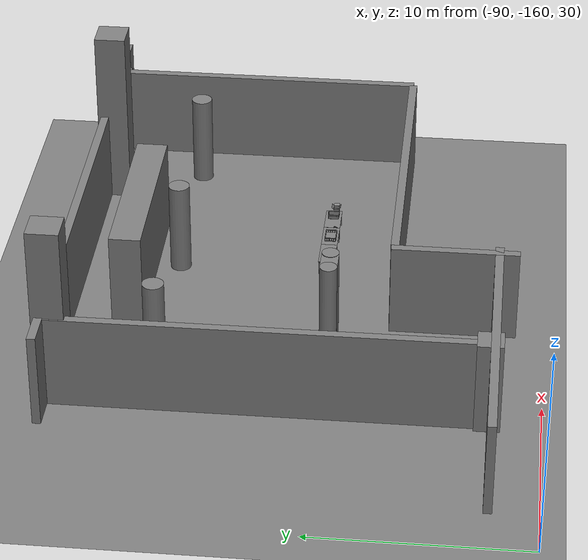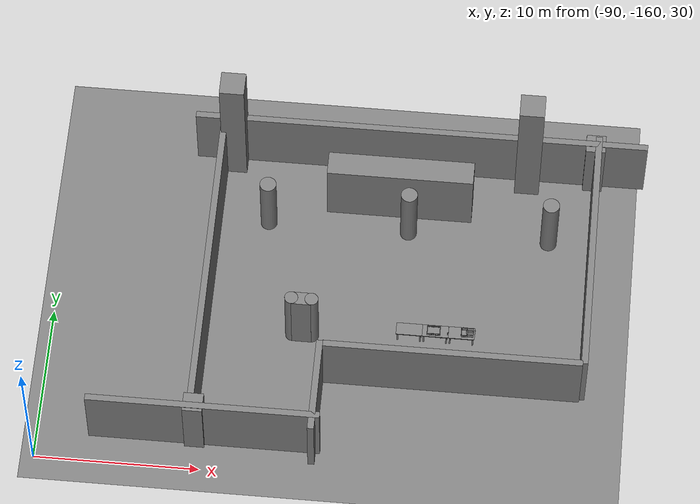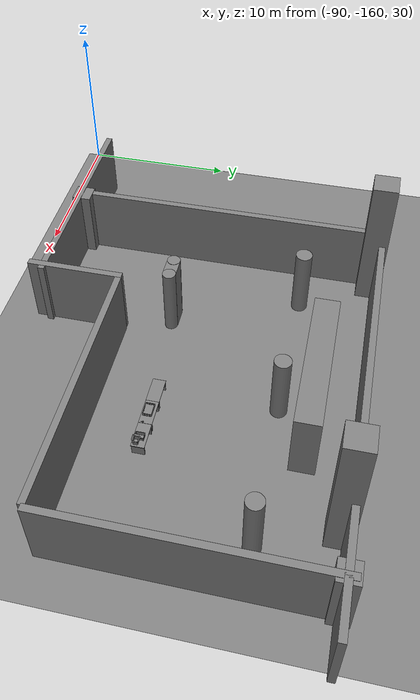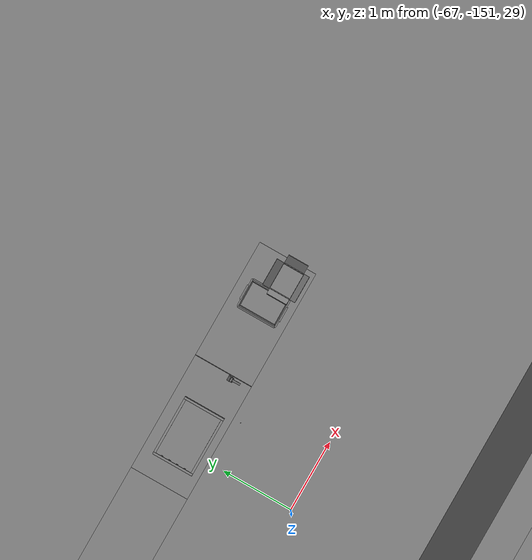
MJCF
<mujoco>
    <option gravity="0.000000000 0.000000000 -9.810000420" timestep="0.0049999999" integrator="implicitfast" density="1.225" viscosity="1.8000001e-05" noslip_iterations="10" iterations="100" sdf_iterations="50">
        <flag multiccd="disable"/>
    </option>
    <size memory="1000M"/>
    <compiler coordinate="local"/>
    <worldbody>
        <light cutoff="30" pos="0 1 1" dir="0 -1 -2"/>
        <light cutoff="30" pos="0 -1 1" dir="0 1 -2"/>
        <body pos="-64.866622925 -149.383972168 30.183746338" euler="89.999992371 89.999946594 0.000000000" name="openloong_gripper_2f85_fix_base_usda_bluebox_01">
            <geom contype="1" conaffinity="1" density="1000" type="box" material="" rgba="0.500000000 0.500000000 0.500000000 1.000000000" solimp="0.899999976 0.949999988 0.001000000" friction="1.000000000 0.005000000 0.000100000" solref="0.020000000 1.000000000" margin="0" condim="3" group="0" pos="0.276596069 0.187225342 0.000061035" quat="0.707107008 0.000077501 0.707106471 0.000077456" size="0.100000001 0.057999998 0.010000000" name="openloong_gripper_2f85_fix_base_usda_geom_705B5F71_910E_475A_B23A_8BBEE9E5E04F"/>
            <geom contype="1" conaffinity="1" density="1000" type="box" material="" rgba="0.500000000 0.500000000 0.500000000 1.000000000" solimp="0.899999976 0.949999988 0.001000000" friction="1.000000000 0.005000000 0.000100000" solref="0.020000000 1.000000000" margin="0" condim="3" group="0" pos="0.000000000 0.002883911 0.000000000" quat="1.000000000 0.000000000 0.000000000 0.000000000" size="0.254000008 0.003000000 0.172000006" name="openloong_gripper_2f85_fix_base_usda_geom_7EB9446B_8E86_4A02_BB90_C4CA26EEC7C0"/>
            <geom contype="1" conaffinity="1" density="1000" type="box" material="" rgba="0.500000000 0.500000000 0.500000000 1.000000000" solimp="0.899999976 0.949999988 0.001000000" friction="1.000000000 0.005000000 0.000100000" solref="0.020000000 1.000000000" margin="0" condim="3" group="0" pos="0.000015259 0.124874115 0.173477173" quat="0.999796450 0.020176515 -0.000000015 0.000000030" size="0.259999990 0.119999997 0.007000000" name="openloong_gripper_2f85_fix_base_usda_geom_1CFB2EAA_96E8_428C_8FB5_1A0788A76BD8"/>
            <geom contype="1" conaffinity="1" density="1000" type="box" material="" rgba="0.500000000 0.500000000 0.500000000 1.000000000" solimp="0.899999976 0.949999988 0.001000000" friction="1.000000000 0.005000000 0.000100000" solref="0.020000000 1.000000000" margin="0" condim="3" group="0" pos="0.000015259 0.124874115 -0.173477173" quat="0.999796450 -0.020176545 -0.000000015 0.000000000" size="0.259999990 0.119999997 0.007000000" name="openloong_gripper_2f85_fix_base_usda_geom_438A1371_791C_4B90_8D79_B1233A7C71A3"/>
            <geom contype="1" conaffinity="1" density="1000" type="box" material="" rgba="0.500000000 0.500000000 0.500000000 1.000000000" solimp="0.899999976 0.949999988 0.001000000" friction="1.000000000 0.005000000 0.000100000" solref="0.020000000 1.000000000" margin="0" condim="3" group="0" pos="0.000015259 0.214012146 0.188980103" quat="0.999913096 0.013176724 0.000000015 0.000000000" size="0.259999990 0.029999999 0.012500000" name="openloong_gripper_2f85_fix_base_usda_geom_DE1EFE59_AF3F_44A4_81BC_C545307E8983"/>
            <geom contype="1" conaffinity="1" density="1000" type="box" material="" rgba="0.500000000 0.500000000 0.500000000 1.000000000" solimp="0.899999976 0.949999988 0.001000000" friction="1.000000000 0.005000000 0.000100000" solref="0.020000000 1.000000000" margin="0" condim="3" group="0" pos="-0.258346558 0.125289917 0.001876831" quat="0.702796996 -0.020792052 0.710783184 0.020769238" size="0.189999998 0.119999997 0.009000000" name="openloong_gripper_2f85_fix_base_usda_geom_DE679EA8_6DE8_4C51_830E_60E4EF0B2744"/>
            <geom contype="1" conaffinity="1" density="1000" type="box" material="" rgba="0.500000000 0.500000000 0.500000000 1.000000000" solimp="0.899999976 0.949999988 0.001000000" friction="1.000000000 0.005000000 0.000100000" solref="0.020000000 1.000000000" margin="0" condim="3" group="0" pos="0.000015259 0.214012146 -0.188980103" quat="0.999913096 -0.013176769 0.000000030 0.000000015" size="0.259999990 0.029999999 0.012500000" name="openloong_gripper_2f85_fix_base_usda_geom_93E15CFD_F4BF_4B09_A0C4_F0925DFA6DC6"/>
            <geom contype="1" conaffinity="1" density="1000" type="box" material="" rgba="0.500000000 0.500000000 0.500000000 1.000000000" solimp="0.899999976 0.949999988 0.001000000" friction="1.000000000 0.005000000 0.000100000" solref="0.020000000 1.000000000" margin="0" condim="3" group="0" pos="-0.276596069 0.187225342 0.000061035" quat="0.707106650 0.000077441 0.707106709 0.000077456" size="0.100000001 0.057999998 0.010000000" name="openloong_gripper_2f85_fix_base_usda_geom_47232757_0ACD_429E_856B_3FD3A68F9446"/>
            <geom contype="1" conaffinity="1" density="1000" type="box" material="" rgba="0.500000000 0.500000000 0.500000000 1.000000000" solimp="0.899999976 0.949999988 0.001000000" friction="1.000000000 0.005000000 0.000100000" solref="0.020000000 1.000000000" margin="0" condim="3" group="0" pos="0.258346558 0.125289917 0.001876831" quat="0.702851534 0.018856451 0.710823834 -0.019329429" size="0.189999998 0.119999997 0.009000000" name="openloong_gripper_2f85_fix_base_usda_geom_096B4B94_3E2E_4F33_8C0E_BD67597873D1"/>
            <freejoint name="openloong_gripper_2f85_fix_base_usda_bluebox_01_joint"/>
            <site size="0.005000000 0.005000000 0.005000000" rgba="0.500000000 0.500000000 0.500000000 1.000000000" pos="0.000000000 0.000000000 0.000000000" quat="0.999961913 0.008726534 0.000000000 0.000000000" group="0" type="sphere" name="openloong_gripper_2f85_fix_base_usda_bluebox_01site"/>
        </body>
        <body pos="-64.496299744 -149.491867065 30.235729218" euler="0.000000000 0.000000000 89.999946594" name="openloong_gripper_2f85_fix_base_usda_cardboardbox_01">
            <geom contype="1" conaffinity="1" density="1000" type="box" material="" rgba="0.500000000 0.500000000 0.500000000 1.000000000" solimp="0.899999976 0.949999988 0.001000000" friction="1.000000000 0.005000000 0.000100000" solref="0.020000000 1.000000000" margin="0" condim="3" group="0" pos="-0.003166199 -0.004086494 0.005052090" quat="1.000000000 0.000000000 0.000000000 0.000000000" size="0.142499998 0.177500010 0.005000000" name="openloong_gripper_2f85_fix_base_usda_geom_A8DE98E9_38A3_4AA7_9003_E3A519C53849"/>
            <geom contype="1" conaffinity="1" density="1000" type="box" material="" rgba="0.500000000 0.500000000 0.500000000 1.000000000" solimp="0.899999976 0.949999988 0.001000000" friction="1.000000000 0.005000000 0.000100000" solref="0.020000000 1.000000000" margin="0" condim="3" group="0" pos="-0.003166199 0.170316696 0.150570869" quat="1.000000000 0.000000000 0.000000000 0.000000000" size="0.142499998 0.005000000 0.149999991" name="openloong_gripper_2f85_fix_base_usda_geom_3A0BE8E2_6843_45A0_BA71_CE1E4D1CC599"/>
            <geom contype="1" conaffinity="1" density="1000" type="box" material="" rgba="0.500000000 0.500000000 0.500000000 1.000000000" solimp="0.899999976 0.949999988 0.001000000" friction="1.000000000 0.005000000 0.000100000" solref="0.020000000 1.000000000" margin="0" condim="3" group="0" pos="-0.147399902 -0.005307198 0.150570869" quat="1.000000000 0.000000000 0.000000000 0.000000000" size="0.005000000 0.177500010 0.149999991" name="openloong_gripper_2f85_fix_base_usda_geom_94B6573B_B509_460B_9F99_4B27A081F103"/>
            <geom contype="1" conaffinity="1" density="1000" type="box" material="" rgba="0.500000000 0.500000000 0.500000000 1.000000000" solimp="0.899999976 0.949999988 0.001000000" friction="1.000000000 0.005000000 0.000100000" solref="0.020000000 1.000000000" margin="0" condim="3" group="0" pos="0.140275955 -0.005307198 0.150570869" quat="1.000000000 0.000000000 0.000000000 0.000000000" size="0.005000000 0.177500010 0.149999991" name="openloong_gripper_2f85_fix_base_usda_geom_549A2FED_2FAA_4A70_9D02_0E1FDF525FD9"/>
            <geom contype="1" conaffinity="1" density="1000" type="box" material="" rgba="0.500000000 0.500000000 0.500000000 1.000000000" solimp="0.899999976 0.949999988 0.001000000" friction="1.000000000 0.005000000 0.000100000" solref="0.020000000 1.000000000" margin="0" condim="3" group="0" pos="-0.003166199 -0.181550980 0.150570869" quat="1.000000000 0.000000000 0.000000000 0.000000000" size="0.142499998 0.005000000 0.149999991" name="openloong_gripper_2f85_fix_base_usda_geom_63C3A551_AC38_40B6_8E20_92177A04495D"/>
            <freejoint name="openloong_gripper_2f85_fix_base_usda_cardboardbox_01_joint"/>
            <site size="0.005000000 0.005000000 0.005000000" rgba="0.500000000 0.500000000 0.500000000 1.000000000" pos="0.000000000 0.000000000 0.000000000" quat="0.999961913 0.008726535 0.000000000 0.000000000" group="0" type="sphere" name="openloong_gripper_2f85_fix_base_usda_site_05D04190_E315_47CC_B5DA_BD516C05DF53"/>
            <body pos="0.139160156 -0.004048347 0.301930904" euler="-179.999954224 49.383502960 179.999954224" name="openloong_gripper_2f85_fix_base_usda_A1_006">
                <geom contype="1" conaffinity="1" density="1000" type="box" material="" rgba="0.500000000 0.500000000 0.500000000 1.000000000" solimp="0.899999976 0.949999988 0.001000000" friction="1.000000000 0.005000000 0.000100000" solref="0.020000000 1.000000000" margin="0" condim="3" group="0" pos="-0.071587563 0.000009537 0.001745224" quat="0.999999881 0.000000000 0.000000000 0.000000000" size="0.071249999 0.179999992 0.002500000" name="openloong_gripper_2f85_fix_base_usda_geom_34E2B4CE_E9DB_41FC_815E_809F4DF98843"/>
                <joint armature="0" stiffness="0.07" damping="0.0099999998" axis="0.000000 1.000000 0.000000" type="hinge" name="openloong_gripper_2f85_fix_base_usda_A1_006"/>
            </body>
            <body pos="-0.145902634 -0.004086494 0.301938057" euler="-180.000000000 -60.000011444 -180.000000000" name="openloong_gripper_2f85_fix_base_usda_A2_006">
                <geom contype="1" conaffinity="1" density="1000" type="box" material="" rgba="0.500000000 0.500000000 0.500000000 1.000000000" solimp="0.899999976 0.949999988 0.001000000" friction="1.000000000 0.005000000 0.000100000" solref="0.020000000 1.000000000" margin="0" condim="3" group="0" pos="0.071268082 0.000009537 0.002717972" quat="0.000002921 0.000000000 -0.000000030 0.999999881" size="0.071249999 0.179999992 0.002500000" name="openloong_gripper_2f85_fix_base_usda_geom_590FE0C9_7EC0_4A42_9D2A_ADE02D9265A4"/>
                <joint armature="0" stiffness="0.07" damping="0.0099999998" axis="0.000000 1.000000 0.000000" type="hinge" name="openloong_gripper_2f85_fix_base_usda_A2_006"/>
            </body>
            <body pos="-0.003385544 0.175991058 0.301930904" euler="-125.858116150 -0.000004561 0.000002331" name="openloong_gripper_2f85_fix_base_usda_B2_006">
                <geom contype="1" conaffinity="1" density="1000" type="box" material="" rgba="0.500000000 0.500000000 0.500000000 1.000000000" solimp="0.899999976 0.949999988 0.001000000" friction="1.000000000 0.005000000 0.000100000" solref="0.020000000 1.000000000" margin="0" condim="3" group="0" pos="0.000009537 -0.070939064 -0.002470016" quat="0.999614120 0.027776197 -0.000000015 0.000000030" size="0.137500003 0.064999998 0.005000000" name="openloong_gripper_2f85_fix_base_usda_geom_46CD6458_D0A9_4EA5_934A_028F7F3F3BB1"/>
                <joint armature="0" stiffness="0.07" damping="0.0099999998" axis="1.000000 0.000000 0.000000" type="hinge" name="openloong_gripper_2f85_fix_base_usda_B2_006"/>
            </body>
            <body pos="-0.003385544 -0.184140205 0.301938057" euler="147.805557251 0.000000000 0.000000000" name="openloong_gripper_2f85_fix_base_usda_B1_006">
                <geom contype="1" conaffinity="1" density="1000" type="box" material="" rgba="0.500000000 0.500000000 0.500000000 1.000000000" solimp="0.899999976 0.949999988 0.001000000" friction="1.000000000 0.005000000 0.000100000" solref="0.020000000 1.000000000" margin="0" condim="3" group="0" pos="-0.000028610 0.070202351 -0.002703667" quat="0.999614179 -0.027776167 0.000000000 0.000000000" size="0.137500003 0.064999998 0.005000000" name="openloong_gripper_2f85_fix_base_usda_geom_31116F44_902E_499C_A8E9_FDAE221599A9"/>
                <joint armature="0" stiffness="0.07" damping="0.0099999998" axis="1.000000 0.000000 0.000000" type="hinge" name="openloong_gripper_2f85_fix_base_usda_B1_006"/>
            </body>
        </body>
        <body pos="-65.882858276 -149.481979370 30.229999542" euler="-64.487716675 0.000000000 0.000000000" name="openloong_gripper_2f85_fix_base_usda_Barcode">
            <geom contype="1" conaffinity="1" density="1000" type="box" material="" rgba="0.500000000 0.500000000 0.500000000 1.000000000" solimp="0.899999976 0.949999988 0.001000000" friction="1.000000000 0.005000000 0.000100000" solref="0.020000000 1.000000000" margin="0" condim="3" group="0" pos="0.000000000 0.013038635 0.001419067" quat="0.000000000 0.000000000 0.000000000 1.000000119" size="0.034000002 0.010000000 0.017999999" name="openloong_gripper_2f85_fix_base_usda_geom_C2637F1F_8631_49E9_A06E_8B34CA71CA90"/>
            <geom contype="1" conaffinity="1" density="1000" type="box" material="" rgba="0.500000000 0.500000000 0.500000000 1.000000000" solimp="0.899999976 0.949999988 0.001000000" friction="1.000000000 0.005000000 0.000100000" solref="0.020000000 1.000000000" margin="0" condim="3" group="0" pos="0.000000000 -0.035301208 -0.007095337" quat="0.000000000 0.000000000 -0.043619365 0.999048233" size="0.028999999 0.010000000 0.020000000" name="openloong_gripper_2f85_fix_base_usda_geom_10526B35_DA67_4F51_A4AD_D337CE1C13E5"/>
            <geom contype="1" conaffinity="1" density="1000" type="box" material="" rgba="0.500000000 0.500000000 0.500000000 1.000000000" solimp="0.899999976 0.949999988 0.001000000" friction="1.000000000 0.005000000 0.000100000" solref="0.020000000 1.000000000" margin="0" condim="3" group="0" pos="0.000000000 -0.043411255 -0.011749268" quat="0.922262907 0.386563420 0.000000000 0.000000000" size="0.026000001 0.010000000 0.020000000" name="openloong_gripper_2f85_fix_base_usda_geom_6EDC3DBF_BB7A_4667_9FC6_EAF22E62E170"/>
            <geom contype="1" conaffinity="1" density="1000" type="box" material="" rgba="0.500000000 0.500000000 0.500000000 1.000000000" solimp="0.899999976 0.949999988 0.001000000" friction="1.000000000 0.005000000 0.000100000" solref="0.020000000 1.000000000" margin="0" condim="3" group="0" pos="0.000000000 -0.016967773 -0.031860352" quat="0.000000000 0.000000000 0.000000000 1.000000119" size="0.008000000 0.010000000 0.013000000" name="openloong_gripper_2f85_fix_base_usda_geom_9A703393_8B30_48F2_A670_6FD66EE33927"/>
            <geom contype="1" conaffinity="1" density="1000" type="box" material="" rgba="0.500000000 0.500000000 0.500000000 1.000000000" solimp="0.899999976 0.949999988 0.001000000" friction="1.000000000 0.005000000 0.000100000" solref="0.020000000 1.000000000" margin="0" condim="3" group="0" pos="0.000000000 -0.001869202 0.000312805" quat="0.953716993 0.300705761 0.000000000 0.000000000" size="0.032000002 0.010000000 0.018999999" name="openloong_gripper_2f85_fix_base_usda_geom_8DFB0764_4DC3_4F27_8FC1_7BFD100CE059"/>
            <geom contype="1" conaffinity="1" density="1000" type="box" material="" rgba="0.500000000 0.500000000 0.500000000 1.000000000" solimp="0.899999976 0.949999988 0.001000000" friction="1.000000000 0.005000000 0.000100000" solref="0.020000000 1.000000000" margin="0" condim="3" group="0" pos="0.000000000 -0.019531250 -0.003173828" quat="0.953716993 0.300705761 0.000000000 0.000000000" size="0.030999999 0.010000000 0.020000000" name="openloong_gripper_2f85_fix_base_usda_geom_6572C7B4_FCA3_4F16_A845_334A0912A2C8"/>
            <geom contype="1" conaffinity="1" density="1000" type="box" material="" rgba="0.500000000 0.500000000 0.500000000 1.000000000" solimp="0.899999976 0.949999988 0.001000000" friction="1.000000000 0.005000000 0.000100000" solref="0.020000000 1.000000000" margin="0" condim="3" group="0" pos="0.000000000 -0.035301208 -0.007095337" quat="0.953716993 0.300705761 0.000000000 0.000000000" size="0.028999999 0.010000000 0.020000000" name="openloong_gripper_2f85_fix_base_usda_geom_FA536F2E_853A_459B_A7C4_2852829A62A0"/>
            <geom contype="1" conaffinity="1" density="1000" type="box" material="" rgba="0.500000000 0.500000000 0.500000000 1.000000000" solimp="0.899999976 0.949999988 0.001000000" friction="1.000000000 0.005000000 0.000100000" solref="0.020000000 1.000000000" margin="0" condim="3" group="0" pos="0.000000000 -0.042617798 -0.071121216" quat="0.000000000 0.000000000 0.000000000 1.000000119" size="0.013000000 0.021000000 0.059999999" name="openloong_gripper_2f85_fix_base_usda_geom_CFA0C22F_4E8A_4AB7_B564_74A2515BED75"/>
            <freejoint name="openloong_gripper_2f85_fix_base_usda_Barcode_joint"/>
            <site size="0.005000000 0.005000000 0.005000000" rgba="0.500000000 0.500000000 0.500000000 1.000000000" pos="0.000000000 0.000000000 0.000000000" quat="1.000000000 0.000000000 0.000000000 0.000000000" group="0" type="sphere" name="openloong_gripper_2f85_fix_base_usda_Barcode_site"/>
        </body>
        <body pos="-66.745018005 -149.392349243 30.184000015" euler="0.000000000 0.000000000 89.999946594" name="[22333056323912]_Basket_01">
            <geom contype="1" conaffinity="1" density="1000" type="box" material="" rgba="0.500000000 0.500000000 0.500000000 1.000000000" solimp="0.899999976 0.949999988 0.001000000" friction="1.000000000 0.005000000 0.000100000" solref="0.020000000 1.000000000" margin="0" condim="3" group="0" pos="-0.052425385 0.389207840 0.089787483" quat="0.707107008 0.000000000 0.000000000 0.707106411" size="0.014249999 0.014249999 0.059999999" name="[22333056323912]_geom_ABCA40CA_4461_45A3_834B_5D32DCA898A1"/>
            <geom contype="1" conaffinity="1" density="1000" type="box" material="" rgba="0.500000000 0.500000000 0.500000000 1.000000000" solimp="0.899999976 0.949999988 0.001000000" friction="1.000000000 0.005000000 0.000100000" solref="0.020000000 1.000000000" margin="0" condim="3" group="0" pos="0.264015198 -0.133043289 0.089787483" quat="0.707107008 0.000000000 0.000000000 0.707106411" size="0.014249999 0.014249999 0.059999999" name="[22333056323912]_geom_0933BFD8_B6BE_44C0_A674_D256A00BF152"/>
            <geom contype="1" conaffinity="1" density="1000" type="box" material="" rgba="0.500000000 0.500000000 0.500000000 1.000000000" solimp="0.899999976 0.949999988 0.001000000" friction="1.000000000 0.005000000 0.000100000" solref="0.020000000 1.000000000" margin="0" condim="3" group="0" pos="-0.264015198 -0.265548706 0.089793205" quat="0.707107008 0.000000000 0.000000000 0.707106411" size="0.014249999 0.014249999 0.059999999" name="[22333056323912]_geom_9B83765A_3207_477D_94AF_089526B1A160"/>
            <geom contype="1" conaffinity="1" density="1000" type="box" material="" rgba="0.500000000 0.500000000 0.500000000 1.000000000" solimp="0.899999976 0.949999988 0.001000000" friction="1.000000000 0.005000000 0.000100000" solref="0.020000000 1.000000000" margin="0" condim="3" group="0" pos="-0.160263062 -0.389322281 0.089793205" quat="0.707107008 0.000000000 0.000000000 0.707106411" size="0.014249999 0.014249999 0.059999999" name="[22333056323912]_geom_A2CA31E6_9428_4E23_A01F_952515386106"/>
            <geom contype="1" conaffinity="1" density="1000" type="box" material="" rgba="0.500000000 0.500000000 0.500000000 1.000000000" solimp="0.899999976 0.949999988 0.001000000" friction="1.000000000 0.005000000 0.000100000" solref="0.020000000 1.000000000" margin="0" condim="3" group="0" pos="0.162265778 -0.389322281 0.089787483" quat="0.707107008 0.000000000 0.000000000 0.707106411" size="0.014249999 0.014249999 0.059999999" name="[22333056323912]_geom_A5324115_A8F5_4628_9BEC_345A4C5E129C"/>
            <geom contype="1" conaffinity="1" density="1000" type="box" material="" rgba="0.500000000 0.500000000 0.500000000 1.000000000" solimp="0.899999976 0.949999988 0.001000000" friction="1.000000000 0.005000000 0.000100000" solref="0.020000000 1.000000000" margin="0" condim="3" group="0" pos="0.264015198 0.389207840 0.089787483" quat="0.707107008 0.000000000 0.000000000 0.707106411" size="0.014249999 0.014249999 0.059999999" name="[22333056323912]_geom_CAB9794E_64D8_4FD5_A508_E6507D8EE8B5"/>
            <geom contype="1" conaffinity="1" density="1000" type="box" material="" rgba="0.500000000 0.500000000 0.500000000 1.000000000" solimp="0.899999976 0.949999988 0.001000000" friction="1.000000000 0.005000000 0.000100000" solref="0.020000000 1.000000000" margin="0" condim="3" group="0" pos="-0.264015198 -0.133043289 0.089793205" quat="0.707107008 0.000000000 0.000000000 0.707106411" size="0.014249999 0.014249999 0.059999999" name="[22333056323912]_geom_665BB1F5_A445_4640_8FE8_4ADA7576276A"/>
            <geom contype="1" conaffinity="1" density="1000" type="box" material="" rgba="0.500000000 0.500000000 0.500000000 1.000000000" solimp="0.899999976 0.949999988 0.001000000" friction="1.000000000 0.005000000 0.000100000" solref="0.020000000 1.000000000" margin="0" condim="3" group="0" pos="-0.264026642 0.269256592 0.089793205" quat="0.707107008 0.000000000 0.000000000 0.707106411" size="0.014249999 0.014249999 0.059999999" name="[22333056323912]_geom_258C303B_E9B0_403A_821C_72F1DD73F814"/>
            <geom contype="1" conaffinity="1" density="1000" type="box" material="" rgba="0.500000000 0.500000000 0.500000000 1.000000000" solimp="0.899999976 0.949999988 0.001000000" friction="1.000000000 0.005000000 0.000100000" solref="0.020000000 1.000000000" margin="0" condim="3" group="0" pos="0.054462433 0.389207840 0.089787483" quat="0.707107008 0.000000000 0.000000000 0.707106411" size="0.014249999 0.014249999 0.059999999" name="[22333056323912]_geom_1C301E5D_4623_44A6_95B8_1F88BB6EA4C1"/>
            <geom contype="1" conaffinity="1" density="1000" type="box" material="" rgba="0.500000000 0.500000000 0.500000000 1.000000000" solimp="0.899999976 0.949999988 0.001000000" friction="1.000000000 0.005000000 0.000100000" solref="0.020000000 1.000000000" margin="0" condim="3" group="0" pos="0.054462433 -0.389322281 0.089787483" quat="0.707107008 0.000000000 0.000000000 0.707106411" size="0.014249999 0.014249999 0.059999999" name="[22333056323912]_geom_01D8F815_B44C_4EF8_A319_60DC66BEC3C5"/>
            <geom contype="1" conaffinity="1" density="1000" type="box" material="" rgba="0.500000000 0.500000000 0.500000000 1.000000000" solimp="0.899999976 0.949999988 0.001000000" friction="1.000000000 0.005000000 0.000100000" solref="0.020000000 1.000000000" margin="0" condim="3" group="0" pos="0.264015198 0.269256592 0.089793205" quat="0.707107008 0.000000000 0.000000000 0.707106411" size="0.014249999 0.014249999 0.059999999" name="[22333056323912]_geom_0041CF58_B12F_46D8_9B62_42BB8E3513AC"/>
            <geom contype="1" conaffinity="1" density="1000" type="box" material="" rgba="0.500000000 0.500000000 0.500000000 1.000000000" solimp="0.899999976 0.949999988 0.001000000" friction="1.000000000 0.005000000 0.000100000" solref="0.020000000 1.000000000" margin="0" condim="3" group="0" pos="0.264015198 -0.389322281 0.089787483" quat="0.707107008 0.000000000 0.000000000 0.707106411" size="0.014249999 0.014249999 0.059999999" name="[22333056323912]_geom_959C5D0A_25D8_4CF6_BB84_99508E9CFB5B"/>
            <geom contype="1" conaffinity="1" density="1000" type="box" material="" rgba="0.500000000 0.500000000 0.500000000 1.000000000" solimp="0.899999976 0.949999988 0.001000000" friction="1.000000000 0.005000000 0.000100000" solref="0.020000000 1.000000000" margin="0" condim="3" group="0" pos="0.000000000 0.000000000 0.015998840" quat="0.707107008 0.000000000 0.000000000 0.707106411" size="0.403499991 0.279000014 0.015750000" name="[22333056323912]_geom_2765D675_F741_41CA_AA63_71174EBF9661"/>
            <geom contype="1" conaffinity="1" density="1000" type="box" material="" rgba="0.500000000 0.500000000 0.500000000 1.000000000" solimp="0.899999976 0.949999988 0.001000000" friction="1.000000000 0.005000000 0.000100000" solref="0.020000000 1.000000000" margin="0" condim="3" group="0" pos="0.000000000 -0.389476776 0.163619041" quat="0.707107008 0.000000000 0.000000000 0.707106411" size="0.015000000 0.277500004 0.015750000" name="[22333056323912]_geom_ACD4FCAE_2AC5_40CC_9784_168111AE16F8"/>
            <geom contype="1" conaffinity="1" density="1000" type="box" material="" rgba="0.500000000 0.500000000 0.500000000 1.000000000" solimp="0.899999976 0.949999988 0.001000000" friction="1.000000000 0.005000000 0.000100000" solref="0.020000000 1.000000000" margin="0" condim="3" group="0" pos="0.162265778 0.389207840 0.089787483" quat="0.707107008 0.000000000 0.000000000 0.707106411" size="0.014249999 0.014249999 0.059999999" name="[22333056323912]_geom_4CE3D538_C4BE_4868_A0B7_BCC2C2E321DC"/>
            <geom contype="1" conaffinity="1" density="1000" type="box" material="" rgba="0.500000000 0.500000000 0.500000000 1.000000000" solimp="0.899999976 0.949999988 0.001000000" friction="1.000000000 0.005000000 0.000100000" solref="0.020000000 1.000000000" margin="0" condim="3" group="0" pos="0.000000000 0.389471054 0.163619041" quat="0.707107008 0.000000000 0.000000000 0.707106411" size="0.015000000 0.277500004 0.015750000" name="[22333056323912]_geom_C067F123_9D88_46B3_AE35_1E0FE0C1B47B"/>
            <geom contype="1" conaffinity="1" density="1000" type="box" material="" rgba="0.500000000 0.500000000 0.500000000 1.000000000" solimp="0.899999976 0.949999988 0.001000000" friction="1.000000000 0.005000000 0.000100000" solref="0.020000000 1.000000000" margin="0" condim="3" group="0" pos="-0.263511658 0.000000000 0.163619041" quat="0.707107008 0.000000000 0.000000000 0.707106411" size="0.403499991 0.015000000 0.015750000" name="[22333056323912]_geom_1E75A037_3635_4941_8916_08434B1B60E5"/>
            <geom contype="1" conaffinity="1" density="1000" type="box" material="" rgba="0.500000000 0.500000000 0.500000000 1.000000000" solimp="0.899999976 0.949999988 0.001000000" friction="1.000000000 0.005000000 0.000100000" solref="0.020000000 1.000000000" margin="0" condim="3" group="0" pos="-0.264015198 0.141334534 0.089793205" quat="0.707107008 0.000000000 0.000000000 0.707106411" size="0.014249999 0.014249999 0.059999999" name="[22333056323912]_geom_95FECB19_4BB0_47E8_B83F_5A6100744299"/>
            <geom contype="1" conaffinity="1" density="1000" type="box" material="" rgba="0.500000000 0.500000000 0.500000000 1.000000000" solimp="0.899999976 0.949999988 0.001000000" friction="1.000000000 0.005000000 0.000100000" solref="0.020000000 1.000000000" margin="0" condim="3" group="0" pos="0.264015198 -0.265548706 0.089787483" quat="0.707107008 0.000000000 0.000000000 0.707106411" size="0.014249999 0.014249999 0.059999999" name="[22333056323912]_geom_473593C6_B770_419A_B457_3D8561A1DD55"/>
            <geom contype="1" conaffinity="1" density="1000" type="box" material="" rgba="0.500000000 0.500000000 0.500000000 1.000000000" solimp="0.899999976 0.949999988 0.001000000" friction="1.000000000 0.005000000 0.000100000" solref="0.020000000 1.000000000" margin="0" condim="3" group="0" pos="-0.160263062 0.389207840 0.089787483" quat="0.707107008 0.000000000 0.000000000 0.707106411" size="0.014249999 0.014249999 0.059999999" name="[22333056323912]_geom_9DC07A57_A2F1_4A04_BF33_87F73240A698"/>
            <geom contype="1" conaffinity="1" density="1000" type="box" material="" rgba="0.500000000 0.500000000 0.500000000 1.000000000" solimp="0.899999976 0.949999988 0.001000000" friction="1.000000000 0.005000000 0.000100000" solref="0.020000000 1.000000000" margin="0" condim="3" group="0" pos="-0.052425385 -0.389322281 0.089787483" quat="0.707107008 0.000000000 0.000000000 0.707106411" size="0.014249999 0.014249999 0.059999999" name="[22333056323912]_geom_1371ADCA_4943_4595_802A_51764BD20982"/>
            <geom contype="1" conaffinity="1" density="1000" type="box" material="" rgba="0.500000000 0.500000000 0.500000000 1.000000000" solimp="0.899999976 0.949999988 0.001000000" friction="1.000000000 0.005000000 0.000100000" solref="0.020000000 1.000000000" margin="0" condim="3" group="0" pos="-0.264026642 -0.389322281 0.089793205" quat="0.707107008 0.000000000 0.000000000 0.707106411" size="0.014249999 0.014249999 0.059999999" name="[22333056323912]_geom_95927F53_0DB7_4C85_9119_AC91CB5F2C6A"/>
            <geom contype="1" conaffinity="1" density="1000" type="box" material="" rgba="0.500000000 0.500000000 0.500000000 1.000000000" solimp="0.899999976 0.949999988 0.001000000" friction="1.000000000 0.005000000 0.000100000" solref="0.020000000 1.000000000" margin="0" condim="3" group="0" pos="0.264015198 0.141334534 0.089787483" quat="0.707107008 0.000000000 0.000000000 0.707106411" size="0.014249999 0.014249999 0.059999999" name="[22333056323912]_geom_8EC132F9_2FFF_4781_8DA8_EAFB6B535055"/>
            <geom contype="1" conaffinity="1" density="1000" type="box" material="" rgba="0.500000000 0.500000000 0.500000000 1.000000000" solimp="0.899999976 0.949999988 0.001000000" friction="1.000000000 0.005000000 0.000100000" solref="0.020000000 1.000000000" margin="0" condim="3" group="0" pos="-0.264015198 0.389207840 0.089793205" quat="0.707107008 0.000000000 0.000000000 0.707106411" size="0.014249999 0.014249999 0.059999999" name="[22333056323912]_geom_E4DCA46E_A5BF_4D2C_80B2_97387287F06C"/>
            <geom contype="1" conaffinity="1" density="1000" type="box" material="" rgba="0.500000000 0.500000000 0.500000000 1.000000000" solimp="0.899999976 0.949999988 0.001000000" friction="1.000000000 0.005000000 0.000100000" solref="0.020000000 1.000000000" margin="0" condim="3" group="0" pos="0.264015198 0.004480362 0.089787483" quat="0.707107008 0.000000000 0.000000000 0.707106411" size="0.014249999 0.014249999 0.059999999" name="[22333056323912]_geom_3DDE7519_6A59_45D4_B59E_1120B857758B"/>
            <geom contype="1" conaffinity="1" density="1000" type="box" material="" rgba="0.500000000 0.500000000 0.500000000 1.000000000" solimp="0.899999976 0.949999988 0.001000000" friction="1.000000000 0.005000000 0.000100000" solref="0.020000000 1.000000000" margin="0" condim="3" group="0" pos="0.263694763 -0.000011444 0.163619041" quat="0.707107008 0.000000000 0.000000000 0.707106411" size="0.403499991 0.015000000 0.015750000" name="[22333056323912]_geom_629F99DE_2A42_4959_9DA6_D2E84CE1B2CC"/>
            <geom contype="1" conaffinity="1" density="1000" type="box" material="" rgba="0.500000000 0.500000000 0.500000000 1.000000000" solimp="0.899999976 0.949999988 0.001000000" friction="1.000000000 0.005000000 0.000100000" solref="0.020000000 1.000000000" margin="0" condim="3" group="0" pos="-0.264015198 0.004480362 0.089793205" quat="0.707107008 0.000000000 0.000000000 0.707106411" size="0.014249999 0.014249999 0.059999999" name="[22333056323912]_geom_7FD81BEB_E051_46A0_A8EF_B209FAA973B1"/>
            <freejoint name="[22333056323912]_joint_B651DE7F_25D6_48A9_A64B_7D08CD0E5A2B"/>
        </body>
        <body pos="0.000000000 0.000000000 0.000000000" euler="0.000000000 0.000000000 0.000000000" name="Static Objects_Static Objects">
            <geom contype="1" conaffinity="1" density="1000" type="box" material="" rgba="0.500000000 0.500000000 0.500000000 1.000000000" solimp="0.899999976 0.949999988 0.001000000" friction="1.000000000 0.005000000 0.000100000" solref="0.020000000 1.000000000" margin="0" condim="3" group="0" pos="-67.544113159 -149.365814209 29.727830887" quat="0.500000417 0.499999970 0.499999553 0.499999970" size="0.381000012 0.319999993 0.041000001" name="Static Objects_geom_30DDDA40_8BCC_47CD_B858_F79797C67F00"/>
            <geom contype="1" conaffinity="1" density="1000" type="box" material="" rgba="0.500000000 0.500000000 0.500000000 1.000000000" solimp="0.899999976 0.949999988 0.001000000" friction="1.000000000 0.005000000 0.000100000" solref="0.020000000 1.000000000" margin="0" condim="3" group="0" pos="-68.239501953 -149.365814209 30.086868286" quat="0.500000417 0.499999970 0.499999553 0.499999970" size="0.370999992 0.039500002 0.745000005" name="Static Objects_geom_6D1573F2_1B49_4009_9FC3_6E89AEAA3EE8"/>
            <geom contype="1" conaffinity="1" density="1000" type="box" material="" rgba="0.500000000 0.500000000 0.500000000 1.000000000" solimp="0.899999976 0.949999988 0.001000000" friction="1.000000000 0.005000000 0.000100000" solref="0.020000000 1.000000000" margin="0" condim="3" group="0" pos="-68.239501953 -149.365814209 30.147235870" quat="0.500000417 0.499999970 0.499999553 0.499999970" size="0.400000006 0.022000000 0.800000012" name="Static Objects_geom_A24F8A2C_2C98_4EBC_A32C_630A50CD9862"/>
            <geom contype="1" conaffinity="1" density="1000" type="box" material="" rgba="0.500000000 0.500000000 0.500000000 1.000000000" solimp="0.899999976 0.949999988 0.001000000" friction="1.000000000 0.005000000 0.000100000" solref="0.020000000 1.000000000" margin="0" condim="3" group="0" pos="-68.934890747 -149.365814209 29.727830887" quat="0.500000417 0.499999970 0.499999553 0.499999970" size="0.381000012 0.319999993 0.041000001" name="Static Objects_geom_C7EA7335_F1A6_473A_AD4C_F73F916608C1"/>
            <geom contype="1" conaffinity="1" density="1000" type="box" material="" rgba="0.500000000 0.500000000 0.500000000 1.000000000" solimp="0.899999976 0.949999988 0.001000000" friction="1.000000000 0.005000000 0.000100000" solref="0.020000000 1.000000000" margin="0" condim="3" group="0" pos="-68.239501953 -149.365814209 29.561563492" quat="0.500000417 0.499999970 0.499999553 0.499999970" size="0.020000000 0.022000000 0.660000026" name="Static Objects_geom_7D8AD89A_0263_4B57_9221_023BADE20032"/>
            <geom contype="1" conaffinity="1" density="1000" type="box" material="" rgba="0.500000000 0.500000000 0.500000000 1.000000000" solimp="0.899999976 0.949999988 0.001000000" friction="1.000000000 0.005000000 0.000100000" solref="0.020000000 1.000000000" margin="0" condim="3" group="0" pos="-65.945671082 -149.365814209 29.727830887" quat="0.500000417 0.499999970 0.499999553 0.499999970" size="0.381000012 0.319999993 0.041000001" name="Static Objects_geom_5638B87F_AA83_4E18_A794_A8531595F402"/>
            <geom contype="1" conaffinity="1" density="1000" type="box" material="" rgba="0.500000000 0.500000000 0.500000000 1.000000000" solimp="0.899999976 0.949999988 0.001000000" friction="1.000000000 0.005000000 0.000100000" solref="0.020000000 1.000000000" margin="0" condim="3" group="0" pos="-66.641059875 -149.365814209 30.086868286" quat="0.500000417 0.499999970 0.499999553 0.499999970" size="0.370999992 0.039500002 0.745000005" name="Static Objects_geom_C77F1D44_5D54_4815_A347_33E138199899"/>
            <geom contype="1" conaffinity="1" density="1000" type="box" material="" rgba="0.500000000 0.500000000 0.500000000 1.000000000" solimp="0.899999976 0.949999988 0.001000000" friction="1.000000000 0.005000000 0.000100000" solref="0.020000000 1.000000000" margin="0" condim="3" group="0" pos="-66.641059875 -149.365814209 30.147235870" quat="0.500000417 0.499999970 0.499999553 0.499999970" size="0.400000006 0.022000000 0.800000012" name="Static Objects_geom_10709C43_A7B9_44DB_8F23_07D95F348975"/>
            <geom contype="1" conaffinity="1" density="1000" type="box" material="" rgba="0.500000000 0.500000000 0.500000000 1.000000000" solimp="0.899999976 0.949999988 0.001000000" friction="1.000000000 0.005000000 0.000100000" solref="0.020000000 1.000000000" margin="0" condim="3" group="0" pos="-67.336448669 -149.365814209 29.727830887" quat="0.500000417 0.499999970 0.499999553 0.499999970" size="0.381000012 0.319999993 0.041000001" name="Static Objects_geom_68B756B3_5EF7_45A3_90BE_20EC75FF02DA"/>
            <geom contype="1" conaffinity="1" density="1000" type="box" material="" rgba="0.500000000 0.500000000 0.500000000 1.000000000" solimp="0.899999976 0.949999988 0.001000000" friction="1.000000000 0.005000000 0.000100000" solref="0.020000000 1.000000000" margin="0" condim="3" group="0" pos="-66.641059875 -149.365814209 29.561563492" quat="0.500000417 0.499999970 0.499999553 0.499999970" size="0.020000000 0.022000000 0.660000026" name="Static Objects_geom_1F0F43D9_27CD_4793_A4A2_327AD2088ACF"/>
            <geom contype="1" conaffinity="1" density="1000" type="box" material="" rgba="0.500000000 0.500000000 0.500000000 1.000000000" solimp="0.899999976 0.949999988 0.001000000" friction="1.000000000 0.005000000 0.000100000" solref="0.020000000 1.000000000" margin="0" condim="3" group="0" pos="-64.338577271 -149.365814209 29.727830887" quat="0.500000417 0.499999970 0.499999553 0.499999970" size="0.381000012 0.319999993 0.041000001" name="Static Objects_geom_386E0960_24B8_426A_B54C_069944E17B67"/>
            <geom contype="1" conaffinity="1" density="1000" type="box" material="" rgba="0.500000000 0.500000000 0.500000000 1.000000000" solimp="0.899999976 0.949999988 0.001000000" friction="1.000000000 0.005000000 0.000100000" solref="0.020000000 1.000000000" margin="0" condim="3" group="0" pos="-65.033966064 -149.365814209 30.086868286" quat="0.500000417 0.499999970 0.499999553 0.499999970" size="0.370999992 0.039500002 0.745000005" name="Static Objects_geom_D09A4DE9_9391_4F6A_90BF_D2E283CFEBC1"/>
            <geom contype="1" conaffinity="1" density="1000" type="box" material="" rgba="0.500000000 0.500000000 0.500000000 1.000000000" solimp="0.899999976 0.949999988 0.001000000" friction="1.000000000 0.005000000 0.000100000" solref="0.020000000 1.000000000" margin="0" condim="3" group="0" pos="-65.033966064 -149.365814209 30.147235870" quat="0.500000417 0.499999970 0.499999553 0.499999970" size="0.400000006 0.022000000 0.800000012" name="Static Objects_geom_A8D2D1B2_13E2_4F7F_886F_8D2A66318A18"/>
            <geom contype="1" conaffinity="1" density="1000" type="box" material="" rgba="0.500000000 0.500000000 0.500000000 1.000000000" solimp="0.899999976 0.949999988 0.001000000" friction="1.000000000 0.005000000 0.000100000" solref="0.020000000 1.000000000" margin="0" condim="3" group="0" pos="-65.729354858 -149.365814209 29.727830887" quat="0.500000417 0.499999970 0.499999553 0.499999970" size="0.381000012 0.319999993 0.041000001" name="Static Objects_geom_E6D03B81_C3E4_44CB_B39D_FBC5DE587EA6"/>
            <geom contype="1" conaffinity="1" density="1000" type="box" material="" rgba="0.500000000 0.500000000 0.500000000 1.000000000" solimp="0.899999976 0.949999988 0.001000000" friction="1.000000000 0.005000000 0.000100000" solref="0.020000000 1.000000000" margin="0" condim="3" group="0" pos="-65.033966064 -149.365814209 29.561563492" quat="0.500000417 0.499999970 0.499999553 0.499999970" size="0.020000000 0.022000000 0.660000026" name="Static Objects_geom_68446E3F_C29F_4191_B201_C803B880D1FC"/>
            <geom contype="1" conaffinity="1" density="1000" type="box" material="" rgba="0.500000000 0.500000000 0.500000000 1.000000000" solimp="0.899999976 0.949999988 0.001000000" friction="1.000000000 0.005000000 0.000100000" solref="0.020000000 1.000000000" margin="0" condim="3" group="0" pos="-61.754566193 -137.853729248 33.906845093" quat="0.707107067 0.000000000 0.000000000 0.707106471" size="0.759999990 0.759999990 4.500000000" name="Static Objects_geom_33FEEBA9_5662_40C4_8030_87AE6806584A"/>
            <geom contype="1" conaffinity="1" density="1000" type="box" material="" rgba="0.500000000 0.500000000 0.500000000 1.000000000" solimp="0.899999976 0.949999988 0.001000000" friction="1.000000000 0.005000000 0.000100000" solref="0.020000000 1.000000000" margin="0" condim="3" group="0" pos="-57.511135101 -144.927108765 31.707921982" quat="1.000000000 0.000000000 0.000000000 0.000000000" size="0.200000003 8.000000000 2.299999952" name="Static Objects_geom_78F915B7_C053_492A_9FE6_2A7BD5CEFCF5"/>
            <geom contype="1" conaffinity="1" density="1000" type="box" material="" rgba="0.500000000 0.500000000 0.500000000 1.000000000" solimp="0.899999976 0.949999988 0.001000000" friction="1.000000000 0.005000000 0.000100000" solref="0.020000000 1.000000000" margin="0" condim="3" group="0" pos="-80.517646790 -157.574050903 31.688196182" quat="0.707107067 0.000000000 0.000000000 0.707106471" size="0.600000024 0.600000024 2.299999952" name="Static Objects_geom_6F27170D_E7C7_4506_8B06_135E2C506544"/>
            <geom contype="1" conaffinity="1" density="1000" type="box" material="" rgba="0.500000000 0.500000000 0.500000000 1.000000000" solimp="0.899999976 0.949999988 0.001000000" friction="1.000000000 0.005000000 0.000100000" solref="0.020000000 1.000000000" margin="0" condim="3" group="0" pos="-80.711044312 -147.414932251 31.666158676" quat="1.000000000 0.000000000 0.000000000 0.000000000" size="0.200000003 10.000000000 2.299999952" name="Static Objects_geom_F45BD0C2_CD88_485C_B9A9_D91306B1F02B"/>
            <geom contype="1" conaffinity="1" density="1000" type="box" material="" rgba="0.500000000 0.500000000 0.500000000 1.000000000" solimp="0.899999976 0.949999988 0.001000000" friction="1.000000000 0.005000000 0.000100000" solref="0.020000000 1.000000000" margin="0" condim="3" group="0" pos="-57.687217712 -137.434692383 31.688196182" quat="0.707107067 0.000000000 0.000000000 0.707106471" size="0.600000024 0.600000024 2.299999952" name="Static Objects_geom_F6E536EB_CF9B_4EA6_96B9_6C49412D7A42"/>
            <geom contype="1" conaffinity="1" density="1000" type="box" material="" rgba="0.500000000 0.500000000 0.500000000 1.000000000" solimp="0.899999976 0.949999988 0.001000000" friction="1.000000000 0.005000000 0.000100000" solref="0.020000000 1.000000000" margin="0" condim="3" group="0" pos="-69.537033081 -140.263229370 31.714921951" quat="0.707107067 0.000000000 0.000000000 0.707106471" size="0.759999990 4.500000000 2.299999952" name="Static Objects_geom_C1019131_C32D_42F4_8B44_C356B6937B7B"/>
            <geom contype="1" conaffinity="1" density="1000" type="box" material="" rgba="0.500000000 0.500000000 0.500000000 1.000000000" solimp="0.899999976 0.949999988 0.001000000" friction="1.000000000 0.005000000 0.000100000" solref="0.020000000 1.000000000" margin="0" condim="3" group="0" pos="-80.073638916 -137.853713989 33.906845093" quat="0.707107067 0.000000000 0.000000000 0.707106471" size="0.759999990 0.759999990 4.500000000" name="Static Objects_geom_2496A17F_A891_480A_A027_BA9118A3C99C"/>
            <geom contype="1" conaffinity="1" density="1000" type="box" material="" rgba="0.500000000 0.500000000 0.500000000 1.000000000" solimp="0.899999976 0.949999988 0.001000000" friction="1.000000000 0.005000000 0.000100000" solref="0.020000000 1.000000000" margin="0" condim="3" group="0" pos="-73.406707764 -155.734664917 31.707921982" quat="1.000000000 0.000000000 0.000000000 0.000000000" size="0.200000003 3.000000000 2.299999952" name="Static Objects_geom_B9C39EB4_B615_4282_89A4_19D0E81A4776"/>
            <geom contype="1" conaffinity="1" density="1000" type="box" material="" rgba="0.500000000 0.500000000 0.500000000 1.000000000" solimp="0.899999976 0.949999988 0.001000000" friction="1.000000000 0.005000000 0.000100000" solref="0.020000000 1.000000000" margin="0" condim="3" group="0" pos="-68.497543335 -137.448257446 31.707921982" quat="0.707107067 0.000000000 0.000000000 0.707106471" size="0.200000003 14.000000000 2.299999952" name="Static Objects_geom_3D945630_72D5_4154_AC01_BE8B23FA8DBB"/>
            <geom contype="1" conaffinity="1" density="1000" type="cylinder" material="" rgba="0.500000000 0.500000000 0.500000000 1.000000000" solimp="0.899999976 0.949999988 0.001000000" friction="1.000000000 0.005000000 0.000100000" solref="0.020000000 1.000000000" margin="0" condim="3" group="0" pos="-68.868522644 -142.134506226 31.711090088" quat="0.707107067 0.000000000 0.000000000 0.707106471" size="0.509999990 2.299999952 1.000000000" name="Static Objects_geom_0940CB91_E995_4F2F_800D_3D6F19FA4EA1"/>
            <geom contype="1" conaffinity="1" density="1000" type="plane" material="" rgba="0.500000000 0.500000000 0.500000000 1.000000000" solimp="0.899999976 0.949999988 0.001000000" friction="1.000000000 0.005000000 0.000100000" solref="0.020000000 1.000000000" margin="0" condim="3" group="0" pos="-72.873703003 -147.131927490 29.409669876" quat="1.000000000 0.000000000 0.000000000 0.000000000" size="18.000000000 14.000000000 1.000000000" name="Static Objects_geom_C8C37DD9_DB5C_4B9C_9CCF_89FD39CA75FB"/>
            <geom contype="1" conaffinity="1" density="1000" type="box" material="" rgba="0.500000000 0.500000000 0.500000000 1.000000000" solimp="0.899999976 0.949999988 0.001000000" friction="1.000000000 0.005000000 0.000100000" solref="0.020000000 1.000000000" margin="0" condim="3" group="0" pos="-79.943580627 -157.782272339 31.707921982" quat="0.707107067 0.000000000 0.000000000 0.707106471" size="0.200000003 7.000000000 2.299999952" name="Static Objects_geom_34AD2866_EB54_4543_ABA0_08245BB81FE3"/>
            <geom contype="1" conaffinity="1" density="1000" type="box" material="" rgba="0.500000000 0.500000000 0.500000000 1.000000000" solimp="0.899999976 0.949999988 0.001000000" friction="1.000000000 0.005000000 0.000100000" solref="0.020000000 1.000000000" margin="0" condim="3" group="0" pos="-65.421028137 -152.903442383 31.707921982" quat="0.707107067 0.000000000 0.000000000 0.707106471" size="0.200000003 7.800000191 2.299999952" name="Static Objects_geom_05E54C7B_8BD5_4689_B2F1_2087F9AC4163"/>
            <geom contype="1" conaffinity="1" density="1000" type="box" material="" rgba="0.500000000 0.500000000 0.500000000 1.000000000" solimp="0.899999976 0.949999988 0.001000000" friction="1.000000000 0.005000000 0.000100000" solref="0.020000000 1.000000000" margin="0" condim="3" group="0" pos="-74.776908875 -149.964416504 31.688196182" quat="1.000000000 0.000000000 0.000000000 0.000000000" size="0.600000024 0.409999996 2.299999952" name="Static Objects_geom_5450CBA1_4698_4C42_B4A4_C24270D80E8C"/>
            <geom contype="1" conaffinity="1" density="1000" type="cylinder" material="" rgba="0.500000000 0.500000000 0.500000000 1.000000000" solimp="0.899999976 0.949999988 0.001000000" friction="1.000000000 0.005000000 0.000100000" solref="0.020000000 1.000000000" margin="0" condim="3" group="0" pos="-60.161884308 -142.134506226 31.711090088" quat="0.707107067 0.000000000 0.000000000 0.707106471" size="0.509999990 2.299999952 1.000000000" name="Static Objects_geom_97D01B9F_6C93_4A88_BC5F_E176EC07DA1F"/>
            <geom contype="1" conaffinity="1" density="1000" type="cylinder" material="" rgba="0.500000000 0.500000000 0.500000000 1.000000000" solimp="0.899999976 0.949999988 0.001000000" friction="1.000000000 0.005000000 0.000100000" solref="0.020000000 1.000000000" margin="0" condim="3" group="0" pos="-75.382453918 -149.963455200 31.711090088" quat="0.707107067 0.000000000 0.000000000 0.707106471" size="0.409999996 2.299999952 1.000000000" name="Static Objects_geom_E9E27302_C4C8_4E8D_BA32_BC2A45D500A7"/>
            <geom contype="1" conaffinity="1" density="1000" type="cylinder" material="" rgba="0.500000000 0.500000000 0.500000000 1.000000000" solimp="0.899999976 0.949999988 0.001000000" friction="1.000000000 0.005000000 0.000100000" solref="0.020000000 1.000000000" margin="0" condim="3" group="0" pos="-74.154960632 -149.963455200 31.711090088" quat="0.707107067 0.000000000 0.000000000 0.707106471" size="0.409999996 2.299999952 1.000000000" name="Static Objects_geom_584FB8BE_FF4B_4EF0_BEE0_D7D74D40B1DB"/>
            <geom contype="1" conaffinity="1" density="1000" type="cylinder" material="" rgba="0.500000000 0.500000000 0.500000000 1.000000000" solimp="0.899999976 0.949999988 0.001000000" friction="1.000000000 0.005000000 0.000100000" solref="0.020000000 1.000000000" margin="0" condim="3" group="0" pos="-77.566612244 -142.134506226 31.711090088" quat="0.707107067 0.000000000 0.000000000 0.707106471" size="0.509999990 2.299999952 1.000000000" name="Static Objects_geom_4E35A802_EB3F_4091_BEAF_89E5DF03B1CD"/>
        </body>
        <body pos="-66.291030884 -149.869689941 29.018842697" euler="0.000000000 0.000000000 89.999946594" mocap="true" name="openloong_gripper_2f85_fix_base_usda_leftHandMocap"/>
        <body pos="-66.291030884 -149.869689941 29.018842697" euler="0.000000000 0.000000000 89.999946594" mocap="true" name="openloong_gripper_2f85_fix_base_usda_rightHandMocap"/>
        <body pos="-66.291030884 -149.869689941 30.218843460" euler="0.000000000 0.000000000 89.999946594" name="openloong_gripper_2f85_fix_base_usda_base_link">
            <geom contype="1" conaffinity="1" density="1000" type="mesh" material="" rgba="0.783999979 0.783999979 0.783999979 1.000000000" solimp="0.899999976 0.949999988 0.001000000" friction="1.000000000 0.005000000 0.000100000" solref="0.020000000 1.000000000" margin="0" condim="3" group="3" mesh="base_link" pos="0.000000000 0.000000000 0.000000000" quat="1.000000000 0.000000000 0.000000000 0.000000000" size="1.000000000 1.000000000 1.000000000" name="openloong_gripper_2f85_fix_base_usda__geom_7_13DA44BF_9EDF_4286_B9DB_170CF1A1153F"/>
            <site size="0.005000000 0.005000000 0.005000000" rgba="0.500000000 0.500000000 0.500000000 1.000000000" pos="0.000000000 0.000000000 0.000000000" quat="1.000000000 0.000000000 0.000000000 0.000000000" group="0" type="sphere" name="openloong_gripper_2f85_fix_base_usda_imu"/>
            <inertial mass="22.447001" pos="-0.005664100 -0.001336700 0.238289997" diaginertia="0.374352545 0.277180195 0.220617250" quat="0.999247074 0.035235517 -0.015086859 0.006023135"/>
            <body pos="0.000000000 0.000000000 0.299997330" euler="0.000000000 0.000000000 0.000000000" name="openloong_gripper_2f85_fix_base_usda_dummy_body">
                <geom contype="1" conaffinity="1" density="1000" type="sphere" material="" rgba="0.783999979 0.783999979 0.783999979 1.000000000" solimp="0.899999976 0.949999988 0.001000000" friction="1.000000000 0.005000000 0.000100000" solref="0.020000000 1.000000000" margin="0" condim="3" group="3" pos="0.000000000 0.000000000 0.000000000" quat="1.000000000 0.000000000 0.000000000 0.000000000" size="0.010000000 0.000000000 0.000000000" name="openloong_gripper_2f85_fix_base_usda__geom_8_5D31C0D3_D321_4C08_A32F_82C4A37C9BCC"/>
                <joint armature="0.0099999998" stiffness="0" damping="0.1" axis="0.000000 0.000000 1.000000" type="hinge" name="openloong_gripper_2f85_fix_base_usda_dummy_joint"/>
                <site size="0.010000000 0.005000000 0.005000000" rgba="0.500000000 0.500000000 0.500000000 1.000000000" pos="0.000000000 0.000000000 0.000000000" quat="1.000000000 0.000000000 0.000000000 0.000000000" group="3" type="sphere" name="openloong_gripper_2f85_fix_base_usda_dummy_site"/>
            </body>
            <body pos="0.009002686 0.000000000 0.406400681" euler="0.000000000 0.000000000 0.000000000" name="openloong_gripper_2f85_fix_base_usda_Link_head_yaw">
                <geom contype="1" conaffinity="1" density="1000" type="mesh" material="" rgba="0.783999979 0.783999979 0.783999979 1.000000000" solimp="0.899999976 0.949999988 0.001000000" friction="1.000000000 0.005000000 0.000100000" solref="0.020000000 1.000000000" margin="0" condim="3" group="3" mesh="Link_head_yaw" pos="0.000000000 0.000000000 0.000000000" quat="1.000000000 0.000000000 0.000000000 0.000000000" size="1.000000000 1.000000000 1.000000000" name="openloong_gripper_2f85_fix_base_usda__geom_10_81EA97A1_F285_4283_A2A7_3C9A55C4411B"/>
                <inertial mass="0.84249002" pos="0.000000000 -0.002081400 0.044801001" diaginertia="0.000700588 0.000629000 0.000553812" quat="0.706933022 -0.015675601 0.015677100 0.706933022"/>
                <body pos="0.000000000 -0.034599304 0.048500061" euler="0.000000000 0.000000000 0.000000000" name="openloong_gripper_2f85_fix_base_usda_Link_head_pitch">
                    <geom contype="1" conaffinity="1" density="1000" type="mesh" material="" rgba="0.783999979 0.783999979 0.783999979 1.000000000" solimp="0.899999976 0.949999988 0.001000000" friction="1.000000000 0.005000000 0.000100000" solref="0.020000000 1.000000000" margin="0" condim="3" group="3" mesh="Link_head_pitch" pos="0.000000000 0.000000000 0.000000000" quat="1.000000000 0.000000000 0.000000000 0.000000000" size="1.000000000 1.000000000 1.000000000" name="openloong_gripper_2f85_fix_base_usda__geom_12_56A3FC73_5A46_47A8_867E_0EE7F641ED93"/>
                    <inertial mass="1.3943" pos="0.020569000 0.033004001 0.125000000" diaginertia="0.006381400 0.006289940 0.004481460" quat="0.973390222 0.008406822 0.228157058 0.019624906"/>
                    <body pos="0.000000000 0.029998779 0.000000000" euler="0.000000000 0.000000000 0.000000000" name="openloong_gripper_2f85_fix_base_usda_neck_center_body">
                        <site size="0.010000000 0.005000000 0.005000000" rgba="0.500000000 0.500000000 0.500000000 1.000000000" pos="0.000000000 0.000000000 0.000000000" quat="1.000000000 0.000000000 0.000000000 0.000000000" group="3" type="sphere" name="openloong_gripper_2f85_fix_base_usda_neck_center_site"/>
                        <body pos="0.020004272 0.000000000 0.149999619" euler="-0.000002229 39.998176575 -90.000205994" name="openloong_gripper_2f85_fix_base_usda_camera_head">
                            <site size="0.010000000 0.005000000 0.005000000" rgba="0.500000000 0.500000000 0.500000000 1.000000000" pos="0.000000000 0.000000000 0.000000000" quat="1.000000000 0.000000000 0.000000000 0.000000000" group="3" type="sphere" name="openloong_gripper_2f85_fix_base_usda_camera_head_site"/>
                        </body>
                    </body>
                </body>
            </body>
            <body pos="0.003997803 -0.161598206 0.392200470" euler="0.000000000 0.000000000 0.000000000" name="openloong_gripper_2f85_fix_base_usda_Link_arm_r_01">
                <geom contype="1" conaffinity="1" density="1000" type="mesh" material="" rgba="0.783999979 0.783999979 0.783999979 1.000000000" solimp="0.899999976 0.949999988 0.001000000" friction="1.000000000 0.005000000 0.000100000" solref="0.020000000 1.000000000" margin="0" condim="3" group="3" mesh="Link_arm_r_01" pos="0.000000000 0.000000000 0.000000000" quat="1.000000000 0.000000000 0.000000000 0.000000000" size="1.000000000 1.000000000 1.000000000" name="openloong_gripper_2f85_fix_base_usda__geom_14_C7FB0399_3588_4489_B9AE_5A56324F6160"/>
                <joint armature="0.0099999998" stiffness="0" damping="1" axis="0.000000 -1.000000 0.000000" limited="true" range="-170.000015259 170.000015259" type="hinge" name="openloong_gripper_2f85_fix_base_usda_J_arm_r_01"/>
                <inertial mass="0.75641" pos="0.004494600 -0.038293999 -0.000001874" diaginertia="0.000842990 0.000803050 0.000587120" quat="-0.000163502 0.707098067 0.000812463 0.707115054"/>
                <body pos="-0.041992188 -0.041000366 0.000000000" euler="0.000000000 0.000000000 0.000000000" name="openloong_gripper_2f85_fix_base_usda_Link_arm_r_02">
                    <geom contype="1" conaffinity="1" density="1000" type="mesh" material="" rgba="0.783999979 0.783999979 0.783999979 1.000000000" solimp="0.899999976 0.949999988 0.001000000" friction="1.000000000 0.005000000 0.000100000" solref="0.020000000 1.000000000" margin="0" condim="3" group="3" mesh="Link_arm_r_02" pos="0.000000000 0.000000000 0.000000000" quat="1.000000000 0.000000000 0.000000000 0.000000000" size="1.000000000 1.000000000 1.000000000" name="openloong_gripper_2f85_fix_base_usda__geom_16_2E822361_E728_4DD7_B33B_BC73CF3F9FE7"/>
                    <joint armature="0.0099999998" stiffness="0" damping="1" axis="-1.000000 0.000000 0.000000" limited="true" range="-105.000244141 105.000244141" type="hinge" name="openloong_gripper_2f85_fix_base_usda_J_arm_r_02"/>
                    <inertial mass="0.98500001" pos="0.041999999 -0.067430697 0.000000000" diaginertia="0.002262690 0.001730990 0.001154020" quat="0.500000000 0.500000000 -0.500000000 0.500000000"/>
                    <body pos="0.041992188 -0.122596741 0.000000000" euler="0.000000000 0.000000000 0.000000000" name="openloong_gripper_2f85_fix_base_usda_Link_arm_r_03">
                        <geom contype="1" conaffinity="1" density="1000" type="mesh" material="" rgba="0.783999979 0.783999979 0.783999979 1.000000000" solimp="0.899999976 0.949999988 0.001000000" friction="1.000000000 0.005000000 0.000100000" solref="0.020000000 1.000000000" margin="0" condim="3" group="3" mesh="Link_arm_r_03" pos="0.000000000 0.000000000 0.000000000" quat="1.000000000 0.000000000 0.000000000 0.000000000" size="1.000000000 1.000000000 1.000000000" name="openloong_gripper_2f85_fix_base_usda__geom_18_7FCA1D9B_5EC6_420F_90A4_33C003589DF1"/>
                        <joint armature="0.0099999998" stiffness="0" damping="1" axis="0.000000 -1.000000 0.000000" limited="true" range="-170.000015259 170.000015259" type="hinge" name="openloong_gripper_2f85_fix_base_usda_J_arm_r_03"/>
                        <inertial mass="0.95899999" pos="-0.001413580 -0.164663002 0.020757901" diaginertia="0.002101340 0.002064590 0.000754802" quat="0.560480952 0.454391927 -0.443732947 0.531497955"/>
                        <body pos="0.035293579 -0.177406311 0.023998260" euler="0.000000000 0.000000000 0.000000000" name="openloong_gripper_2f85_fix_base_usda_Link_arm_r_04">
                            <geom contype="1" conaffinity="1" density="1000" type="mesh" material="" rgba="0.783999979 0.783999979 0.783999979 1.000000000" solimp="0.899999976 0.949999988 0.001000000" friction="1.000000000 0.005000000 0.000100000" solref="0.020000000 1.000000000" margin="0" condim="3" group="3" mesh="Link_arm_r_04" pos="0.000000000 0.000000000 0.000000000" quat="1.000000000 0.000000000 0.000000000 0.000000000" size="1.000000000 1.000000000 1.000000000" name="openloong_gripper_2f85_fix_base_usda__geom_20_B5643F6D_B547_4D96_A115_AF31AECE4A10"/>
                            <joint armature="0.0099999998" stiffness="0" damping="1" axis="-1.000000 0.000000 0.000000" limited="true" range="0.000000000 170.000015259" type="hinge" name="openloong_gripper_2f85_fix_base_usda_J_arm_r_04"/>
                            <inertial mass="0.60000002" pos="-0.038727000 -0.060766999 -0.021003000" diaginertia="0.001092610 0.000712422 0.000645102" quat="0.327701002 0.632602990 -0.467366993 0.523443997"/>
                            <body pos="-0.035293579 -0.103492737 -0.023998260" euler="0.000000000 0.000000000 0.000000000" name="openloong_gripper_2f85_fix_base_usda_Link_arm_r_05">
                                <geom contype="1" conaffinity="1" density="1000" type="mesh" material="" rgba="0.783999979 0.783999979 0.783999979 1.000000000" solimp="0.899999976 0.949999988 0.001000000" friction="1.000000000 0.005000000 0.000100000" solref="0.020000000 1.000000000" margin="0" condim="3" group="3" mesh="Link_arm_r_05" pos="0.000000000 0.000000000 0.000000000" quat="1.000000000 0.000000000 0.000000000 0.000000000" size="1.000000000 1.000000000 1.000000000" name="openloong_gripper_2f85_fix_base_usda__geom_22_B7F4BAD6_1E82_4DC5_99B8_1B4F6D0F065C"/>
                                <joint armature="0.0099999998" stiffness="0" damping="1" axis="0.000000 -1.000000 0.000000" limited="true" range="-170.000015259 170.000015259" type="hinge" name="openloong_gripper_2f85_fix_base_usda_J_arm_r_05"/>
                                <inertial mass="0.68976003" pos="0.000032712 -0.068658002 -0.000111780" diaginertia="0.002522510 0.002411100 0.000448695" quat="0.707660973 0.706543028 -0.002603360 0.002470550"/>
                                <body pos="-0.026489258 -0.196502686 0.000000000" euler="0.000000000 0.000000000 0.000000000" name="openloong_gripper_2f85_fix_base_usda_Link_arm_r_06">
                                    <geom contype="1" conaffinity="1" density="1000" type="mesh" material="" rgba="0.783999979 0.783999979 0.783999979 1.000000000" solimp="0.899999976 0.949999988 0.001000000" friction="1.000000000 0.005000000 0.000100000" solref="0.020000000 1.000000000" margin="0" condim="3" group="3" mesh="Link_arm_r_06" pos="0.000000000 0.000000000 0.000000000" quat="1.000000000 0.000000000 0.000000000 0.000000000" size="1.000000000 1.000000000 1.000000000" name="openloong_gripper_2f85_fix_base_usda__geom_24_BDACC0D5_CFA4_489F_BFE1_DA4C58C96590"/>
                                    <joint armature="0.0099999998" stiffness="0" damping="1" axis="1.000000 0.000000 0.000000" limited="true" range="-105.000244141 105.000244141" type="hinge" name="openloong_gripper_2f85_fix_base_usda_J_arm_r_06"/>
                                    <inertial mass="0.28" pos="0.026078001 -0.000000896 0.001663700" diaginertia="0.000156930 0.000145601 0.000104979" quat="0.707080841 0.001851080 0.001883810 0.707127810"/>
                                    <body pos="0.026489258 0.000000000 0.031799316" euler="0.000000000 0.000000000 0.000000000" name="openloong_gripper_2f85_fix_base_usda_Link_arm_r_07">
                                        <geom contype="1" conaffinity="1" density="1000" type="mesh" material="" rgba="0.783999979 0.783999979 0.783999979 1.000000000" solimp="0.899999976 0.949999988 0.001000000" friction="1.000000000 0.005000000 0.000100000" solref="0.020000000 1.000000000" margin="0" condim="3" group="3" mesh="Link_arm_r_07" pos="0.000000000 0.000000000 0.000000000" quat="1.000000000 0.000000000 0.000000000 0.000000000" size="1.000000000 1.000000000 1.000000000" name="openloong_gripper_2f85_fix_base_usda__geom_26_6F76F4B7_F015_4F77_AA72_3CBFBDE3FBF0"/>
                                        <joint armature="0.0099999998" stiffness="0" damping="1" axis="0.000000 0.000000 1.000000" limited="true" range="-60.000133514 60.000133514" type="hinge" name="openloong_gripper_2f85_fix_base_usda_J_arm_r_07"/>
                                        <inertial mass="0.61353999" pos="-0.007859000 -0.158170000 -0.027736001" diaginertia="0.003037610 0.002570910 0.000729379" quat="0.427542925 0.443532884 -0.553093910 0.560867906"/>
                                        <body pos="0.000000000 0.286994934 -0.270000458" euler="150.000350952 -0.000001649 -0.000000442" name="openloong_gripper_2f85_fix_base_usda_camera_wrist_r">
                                            <site size="0.010000000 0.005000000 0.005000000" rgba="0.500000000 0.500000000 0.500000000 1.000000000" pos="0.000000000 0.000000000 0.000000000" quat="1.000000000 0.000000000 0.000000000 0.000000000" group="3" type="sphere" name="openloong_gripper_2f85_fix_base_usda_camera_wrist_r_site"/>
                                        </body>
                                        <body pos="0.000000000 -0.220008850 -0.033002853" euler="0.000000000 0.000000000 179.999969482" name="openloong_gripper_2f85_fix_base_usda_ee_center_body_r">
                                            <site size="0.010000000 0.005000000 0.005000000" rgba="0.500000000 0.500000000 0.500000000 1.000000000" pos="0.000000000 0.000000000 0.000000000" quat="1.000000000 0.000000000 0.000000000 0.000000000" group="3" type="sphere" name="openloong_gripper_2f85_fix_base_usda_ee_center_site_r"/>
                                        </body>
                                        <body pos="0.000000000 -0.066001892 -0.031000137" euler="89.999984741 0.000000000 180.000000000" name="openloong_gripper_2f85_fix_base_usda_zbr_base_link">
                                            <geom contype="1" conaffinity="1" density="1000" type="mesh" material="" rgba="0.783999979 0.783999979 0.783999979 1.000000000" solimp="0.899999976 0.949999988 0.001000000" friction="1.000000000 0.005000000 0.000100000" solref="0.020000000 1.000000000" margin="0" condim="3" group="3" mesh="base" pos="0.000000000 0.000003815 -0.000007629" quat="1.000000000 0.000000000 0.000000000 0.000000000" size="1.000000238 1.000000238 1.000000238" name="openloong_gripper_2f85_fix_base_usda__geom_30_EAF503A8_D691_49A5_8F8F_F385AC347CA3"/>
                                            <inertial mass="0.77744102" pos="0.000000000 -0.000027039 0.035467502" diaginertia="0.000260285 0.000225381 0.000152708" quat="0.999998808 -0.001528488 0.000000000 0.000000000"/>
                                            <body pos="-0.030609138 0.004745484 0.065696731" euler="-89.999984741 -0.000000000 0.000000000" name="openloong_gripper_2f85_fix_base_usda_r_left_driver">
                                                <geom contype="1" conaffinity="1" density="1000" type="mesh" material="" rgba="0.783999979 0.783999979 0.783999979 1.000000000" solimp="0.899999976 0.949999988 0.001000000" friction="1.000000000 0.005000000 0.000100000" solref="0.020000000 1.000000000" margin="0" condim="3" group="3" mesh="driver" pos="0.030609138 0.054901138 -0.004699708" quat="0.707106829 0.707106709 0.000000000 -0.000000000" size="1.000000238 1.000000238 1.000000238" name="openloong_gripper_2f85_fix_base_usda__geom_32_6FE6BE06_5952_40F5_A3A6_02E3FC9B52C8"/>
                                                <joint armature="0.0049999999" stiffness="0" damping="0.1" axis="0.000000 0.000000 1.000000" limited="true" range="0.000000000 51.566200256" type="hinge" name="openloong_gripper_2f85_fix_base_usda_r_left_driver_joint"/>
                                                <inertial mass="0.0089956298" pos="0.000000000 0.017754700 0.001073140" diaginertia="0.000001724 0.000001609 0.000000322" quat="0.681301236 0.732003212 0.000000000 0.000000000"/>
                                                <body pos="-0.031402595 0.004524232 -0.010200503" euler="0.000000000 0.000000000 180.000000000" name="openloong_gripper_2f85_fix_base_usda_r_left_coupler">
                                                    <geom contype="1" conaffinity="1" density="1000" type="mesh" material="" rgba="0.783999979 0.783999979 0.783999979 1.000000000" solimp="0.899999976 0.949999988 0.001000000" friction="1.000000000 0.005000000 0.000100000" solref="0.020000000 1.000000000" margin="0" condim="3" group="3" mesh="coupler" pos="-0.062011734 -0.050354015 0.005500795" quat="0.707106829 -0.707106709 0.000000000 -0.000000000" size="1.000000238 1.000000238 1.000000238" name="openloong_gripper_2f85_fix_base_usda__geom_34_5980ADCD_F653_4BD5_84F2_77F6852F1BBC"/>
                                                    <inertial mass="0.0140974" pos="0.000000000 0.003012090 0.023217499" diaginertia="0.000004162 0.000003522 0.000000888" quat="0.705635548 -0.045590367 0.045590367 0.705635548"/>
                                                </body>
                                            </body>
                                            <body pos="-0.012695315 -0.012001040 0.072212234" euler="-89.999984741 -0.000000000 0.000000000" name="openloong_gripper_2f85_fix_base_usda_r_left_spring_link">
                                                <geom contype="1" conaffinity="1" density="1000" type="mesh" material="" rgba="0.783999979 0.783999979 0.783999979 1.000000000" solimp="0.899999976 0.949999988 0.001000000" friction="1.000000000 0.005000000 0.000100000" solref="0.020000000 1.000000000" margin="0" condim="3" group="3" mesh="spring_link" pos="0.012695315 0.061416641 0.012050631" quat="0.707106829 0.707106709 0.000000000 -0.000000000" size="1.000000238 1.000000238 1.000000238" name="openloong_gripper_2f85_fix_base_usda__geom_36_8274F6AB_A344_4868_901B_C8128671BE76"/>
                                                <joint armature="0.001" stiffness="0.050000001" damping="0.00125" axis="0.000000 0.000000 1.000000" limited="true" range="-17.000000000 51.566200256" type="hinge" name="openloong_gripper_2f85_fix_base_usda_r_left_spring_link_joint"/>
                                                <inertial mass="0.0221642" pos="-0.000000009 0.018162400 0.021265799" diaginertia="0.000008969 0.000006717 0.000002639" quat="0.663403213 -0.244737089 0.244737089 0.663403213"/>
                                                <body pos="-0.038208015 -0.042503368 0.002950669" euler="180.000000000 0.000000000 -0.002185660" name="openloong_gripper_2f85_fix_base_usda_r_left_follower">
                                                    <geom contype="1" conaffinity="1" density="1000" type="mesh" material="" rgba="0.783999979 0.783999979 0.783999979 1.000000000" solimp="0.899999976 0.949999988 0.001000000" friction="1.000000000 0.005000000 0.000100000" solref="0.020000000 1.000000000" margin="0" condim="3" group="3" mesh="tongue" pos="0.050918590 -0.103920005 -0.009099962" quat="0.707106829 -0.707106709 0.000000030 0.000000030" size="1.000000238 1.000000238 1.000000238" name="openloong_gripper_2f85_fix_base_usda__geom_40_0CE2EF7C_B435_4EE6_BF9A_6147DFE14456"/>
                                                    <geom contype="1" conaffinity="1" density="1000" type="mesh" material="" rgba="0.783999979 0.783999979 0.783999979 1.000000000" solimp="0.899999976 0.949999988 0.001000000" friction="1.000000000 0.005000000 0.000100000" solref="0.020000000 1.000000000" margin="0" condim="3" group="3" mesh="follower" pos="0.050918590 -0.103920005 -0.009099962" quat="0.707106829 -0.707106709 0.000000030 0.000000030" size="1.000000238 1.000000238 1.000000238" name="openloong_gripper_2f85_fix_base_usda__geom_39_F6D9F04B_15DE_478A_B55F_383CDC0E1DAB"/>
                                                    <joint armature="0.001" stiffness="0" damping="0.1" axis="0.000000 0.000000 1.000000" limited="true" range="-49.999961853 51.566200256" type="hinge" name="openloong_gripper_2f85_fix_base_usda_r_left_follower"/>
                                                    <inertial mass="0.0125222" pos="0.000000000 -0.011046000 0.012478600" diaginertia="0.000002674 0.000002456 0.000000602" quat="0.986436546 0.164143041 0.000000000 0.000000000"/>
                                                    <body pos="-0.037765510 -0.103912376 -0.009099962" euler="-89.999984741 0.000000000 0.000004829" name="openloong_gripper_2f85_fix_base_usda_r_left_pad">
                                                        <geom contype="1" conaffinity="1" density="1000" type="box" material="" rgba="0.550000012 0.550000012 0.550000012 1.000000000" solimp="0.949999988 0.990000010 0.001000000" friction="0.699999988 0.005000000 0.000100000" solref="0.020000000 1.000000000" margin="0" condim="3" group="3" mass="1e-06" pos="0.043243419 0.000003815 0.119995147" quat="0.999999881 0.000000000 0.000000000 0.000000000" size="0.002000001 0.011000003 0.009375002" name="openloong_gripper_2f85_fix_base_usda_r_left_pad1_6D09E2EC_70CF_46DA_A6B0_B0ED5D2B67C6"/>
                                                        <geom contype="1" conaffinity="1" density="1000" type="box" material="" rgba="0.449999988 0.449999988 0.449999988 1.000000000" solimp="0.949999988 0.990000010 0.001000000" friction="0.600000024 0.005000000 0.000100000" solref="0.020000000 1.000000000" margin="0" condim="3" group="3" mass="1e-06" pos="0.043243419 0.000003815 0.138748199" quat="0.999999881 0.000000000 0.000000000 0.000000000" size="0.002000001 0.011000003 0.009375002" name="openloong_gripper_2f85_fix_base_usda_r_left_pad2_BDF9F067_239C_4A93_B1A4_BDFB06EAB47C"/>
                                                    </body>
                                                </body>
                                            </body>
                                            <body pos="0.030593880 -0.004753114 0.065696731" euler="89.999984741 0.000000000 180.000000000" name="openloong_gripper_2f85_fix_base_usda_r_right_driver">
                                                <geom contype="1" conaffinity="1" density="1000" type="mesh" material="" rgba="0.783999979 0.783999979 0.783999979 1.000000000" solimp="0.899999976 0.949999988 0.001000000" friction="1.000000000 0.005000000 0.000100000" solref="0.020000000 1.000000000" margin="0" condim="3" group="3" mesh="driver" pos="0.030593880 0.054901138 -0.004699708" quat="0.707106829 0.707106709 0.000000000 0.000000000" size="1.000000238 1.000000238 1.000000238" name="openloong_gripper_2f85_fix_base_usda__geom_42_E30891B6_B40A_433A_92B2_EDBE794E1797"/>
                                                <joint armature="0.0049999999" stiffness="0" damping="0.1" axis="0.000000 0.000000 1.000000" limited="true" range="0.000000000 51.566200256" type="hinge" name="openloong_gripper_2f85_fix_base_usda_r_right_driver_joint"/>
                                                <inertial mass="0.0089956298" pos="0.000000000 0.017754700 0.001073140" diaginertia="0.000001724 0.000001609 0.000000322" quat="0.681301236 0.732003212 0.000000000 0.000000000"/>
                                                <body pos="-0.031417854 0.004531861 -0.010202411" euler="0.000000000 0.000000000 180.000000000" name="openloong_gripper_2f85_fix_base_usda_r_right_coupler">
                                                    <geom contype="1" conaffinity="1" density="1000" type="mesh" material="" rgba="0.783999979 0.783999979 0.783999979 1.000000000" solimp="0.899999976 0.949999988 0.001000000" friction="1.000000000 0.005000000 0.000100000" solref="0.020000000 1.000000000" margin="0" condim="3" group="3" mesh="coupler" pos="-0.062042251 -0.050376903 0.005500795" quat="0.707106829 -0.707106709 0.000000000 0.000000000" size="1.000000238 1.000000238 1.000000238" name="openloong_gripper_2f85_fix_base_usda__geom_44_69E7FE62_6E3C_4D6F_99E9_B7342B6581B4"/>
                                                    <inertial mass="0.0140974" pos="0.000000000 0.003012090 0.023217499" diaginertia="0.000004162 0.000003522 0.000000888" quat="0.705635548 -0.045590367 0.045590367 0.705635548"/>
                                                </body>
                                            </body>
                                            <body pos="0.012695315 0.011997226 0.072219864" euler="89.999984741 0.000000000 180.000000000" name="openloong_gripper_2f85_fix_base_usda_r_right_spring_link">
                                                <geom contype="1" conaffinity="1" density="1000" type="mesh" material="" rgba="0.783999979 0.783999979 0.783999979 1.000000000" solimp="0.899999976 0.949999988 0.001000000" friction="1.000000000 0.005000000 0.000100000" solref="0.020000000 1.000000000" margin="0" condim="3" group="3" mesh="spring_link" pos="0.012695315 0.061424270 0.012048724" quat="0.707106829 0.707106709 0.000000000 0.000000000" size="1.000000238 1.000000238 1.000000238" name="openloong_gripper_2f85_fix_base_usda__geom_46_BF4A1585_18C7_4383_B56E_49412FBE6987"/>
                                                <joint armature="0.001" stiffness="0.050000001" damping="0.00125" axis="0.000000 0.000000 1.000000" limited="true" range="-17.000000000 51.566200256" type="hinge" name="openloong_gripper_2f85_fix_base_usda_r_right_spring_link_joint"/>
                                                <inertial mass="0.0221642" pos="-0.000000009 0.018162400 0.021265799" diaginertia="0.000008969 0.000006717 0.000002639" quat="0.663403213 -0.244737089 0.244737089 0.663403213"/>
                                                <body pos="-0.038208015 -0.042495739 0.002950669" euler="180.000000000 0.000000000 0.000000000" name="openloong_gripper_2f85_fix_base_usda_r_right_follower">
                                                    <geom contype="1" conaffinity="1" density="1000" type="mesh" material="" rgba="0.783999979 0.783999979 0.783999979 1.000000000" solimp="0.899999976 0.949999988 0.001000000" friction="1.000000000 0.005000000 0.000100000" solref="0.020000000 1.000000000" margin="0" condim="3" group="3" mesh="follower" pos="0.050888073 -0.103927635 -0.009099962" quat="0.707106829 -0.707106709 0.000000000 0.000000000" size="1.000000238 1.000000238 1.000000238" name="openloong_gripper_2f85_fix_base_usda__geom_50_6524AEC9_1A41_422D_80F9_B0B036C2A88F"/>
                                                    <geom contype="1" conaffinity="1" density="1000" type="mesh" material="" rgba="0.783999979 0.783999979 0.783999979 1.000000000" solimp="0.899999976 0.949999988 0.001000000" friction="1.000000000 0.005000000 0.000100000" solref="0.020000000 1.000000000" margin="0" condim="3" group="3" mesh="tongue" pos="0.050888073 -0.103927635 -0.009099962" quat="0.707106829 -0.707106709 0.000000000 0.000000000" size="1.000000238 1.000000238 1.000000238" name="openloong_gripper_2f85_fix_base_usda__geom_49_ED7B8CE8_E114_4476_9FF1_7489E0A664EB"/>
                                                    <joint armature="0.001" stiffness="0" damping="0.1" axis="0.000000 0.000000 1.000000" limited="true" range="-49.999961853 51.566200256" type="hinge" name="openloong_gripper_2f85_fix_base_usda_r_right_follower_joint"/>
                                                    <inertial mass="0.0125222" pos="0.000000000 -0.011046000 0.012478600" diaginertia="0.000002674 0.000002456 0.000000602" quat="0.986436546 0.164143041 0.000000000 0.000000000"/>
                                                    <body pos="-0.037811287 -0.103927635 -0.009099962" euler="-89.999984741 0.000000000 0.000000000" name="openloong_gripper_2f85_fix_base_usda_r_right_pad">
                                                        <geom contype="1" conaffinity="1" density="1000" type="box" material="" rgba="0.449999988 0.449999988 0.449999988 1.000000000" solimp="0.949999988 0.990000010 0.001000000" friction="0.600000024 0.005000000 0.000100000" solref="0.020000000 1.000000000" margin="0" condim="3" group="3" mass="1e-06" pos="0.043258678 0.000000000 0.138748199" quat="1.000000000 0.000000000 0.000000000 0.000000000" size="0.002000001 0.011000003 0.009375002" name="openloong_gripper_2f85_fix_base_usda_r_right_pad2_EA498FE0_A9AF_47F0_A34D_3164F13A3399"/>
                                                        <geom contype="1" conaffinity="1" density="1000" type="box" material="" rgba="0.550000012 0.550000012 0.550000012 1.000000000" solimp="0.949999988 0.990000010 0.001000000" friction="0.699999988 0.005000000 0.000100000" solref="0.020000000 1.000000000" margin="0" condim="3" group="3" mass="1e-06" pos="0.043258678 0.000003815 0.120002776" quat="1.000000000 0.000000000 0.000000000 0.000000000" size="0.002000001 0.011000003 0.009375002" name="openloong_gripper_2f85_fix_base_usda_r_right_pad1_F7683650_4337_49A7_A299_EB81A4078319"/>
                                                    </body>
                                                </body>
                                            </body>
                                        </body>
                                    </body>
                                </body>
                            </body>
                        </body>
                    </body>
                </body>
            </body>
            <body pos="0.003997803 0.161590576 0.392200470" euler="0.000000000 0.000000000 0.000000000" name="openloong_gripper_2f85_fix_base_usda_Link_arm_l_01">
                <geom contype="1" conaffinity="1" density="1000" type="mesh" material="" rgba="0.783999979 0.783999979 0.783999979 1.000000000" solimp="0.899999976 0.949999988 0.001000000" friction="1.000000000 0.005000000 0.000100000" solref="0.020000000 1.000000000" margin="0" condim="3" group="3" mesh="Link_arm_l_01" pos="0.000000000 0.000000000 0.000000000" quat="1.000000000 0.000000000 0.000000000 0.000000000" size="1.000000000 1.000000000 1.000000000" name="openloong_gripper_2f85_fix_base_usda__geom_52_737F18F6_485C_475D_9466_C148B8CAB174"/>
                <joint armature="0.0099999998" stiffness="0" damping="1" axis="0.000000 1.000000 0.000000" limited="true" range="-170.000015259 170.000015259" type="hinge" name="openloong_gripper_2f85_fix_base_usda_J_arm_l_01"/>
                <inertial mass="0.75640601" pos="-0.004494650 0.038294200 -0.000001874" diaginertia="0.000842986 0.000803053 0.000587115" quat="-0.000812496 0.707115054 0.000163424 0.707098067"/>
                <body pos="0.042007446 0.041000366 0.000000000" euler="0.000000000 0.000000000 0.000000000" name="openloong_gripper_2f85_fix_base_usda_Link_arm_l_02">
                    <geom contype="1" conaffinity="1" density="1000" type="mesh" material="" rgba="0.783999979 0.783999979 0.783999979 1.000000000" solimp="0.899999976 0.949999988 0.001000000" friction="1.000000000 0.005000000 0.000100000" solref="0.020000000 1.000000000" margin="0" condim="3" group="3" mesh="Link_arm_l_02" pos="0.000000000 0.000000000 0.000000000" quat="1.000000000 0.000000000 0.000000000 0.000000000" size="1.000000000 1.000000000 1.000000000" name="openloong_gripper_2f85_fix_base_usda__geom_54_77B55351_DBFE_43D2_9600_5CB96C398277"/>
                    <joint armature="0.0099999998" stiffness="0" damping="1" axis="-1.000000 0.000000 0.000000" limited="true" range="-105.000244141 105.000244141" type="hinge" name="openloong_gripper_2f85_fix_base_usda_J_arm_l_02"/>
                    <inertial mass="0.98500001" pos="-0.041999999 0.067430697 0.000000000" diaginertia="0.002262690 0.001730990 0.001154020" quat="0.500000000 0.500000000 -0.500000000 0.500000000"/>
                    <body pos="-0.042007446 0.122596741 0.000000000" euler="0.000000000 0.000000000 0.000000000" name="openloong_gripper_2f85_fix_base_usda_Link_arm_l_03">
                        <geom contype="1" conaffinity="1" density="1000" type="mesh" material="" rgba="0.783999979 0.783999979 0.783999979 1.000000000" solimp="0.899999976 0.949999988 0.001000000" friction="1.000000000 0.005000000 0.000100000" solref="0.020000000 1.000000000" margin="0" condim="3" group="3" mesh="Link_arm_l_03" pos="0.000000000 0.000000000 0.000000000" quat="1.000000000 0.000000000 0.000000000 0.000000000" size="1.000000000 1.000000000 1.000000000" name="openloong_gripper_2f85_fix_base_usda__geom_56_DD8B1FF8_7207_40DA_AC5B_9E3A8A4E1952"/>
                        <joint armature="0.0099999998" stiffness="0" damping="1" axis="0.000000 1.000000 0.000000" limited="true" range="-170.000015259 170.000015259" type="hinge" name="openloong_gripper_2f85_fix_base_usda_J_arm_l_03"/>
                        <inertial mass="0.95899999" pos="0.001413580 0.164663002 0.020757901" diaginertia="0.002101340 0.002064590 0.000754802" quat="0.443732947 0.531497955 -0.560480952 0.454391927"/>
                        <body pos="-0.035293579 0.177406311 0.023998260" euler="0.000000000 0.000000000 0.000000000" name="openloong_gripper_2f85_fix_base_usda_Link_arm_l_04">
                            <geom contype="1" conaffinity="1" density="1000" type="mesh" material="" rgba="0.783999979 0.783999979 0.783999979 1.000000000" solimp="0.899999976 0.949999988 0.001000000" friction="1.000000000 0.005000000 0.000100000" solref="0.020000000 1.000000000" margin="0" condim="3" group="3" mesh="Link_arm_l_04" pos="0.000000000 0.000000000 0.000000000" quat="1.000000000 0.000000000 0.000000000 0.000000000" size="1.000000000 1.000000000 1.000000000" name="openloong_gripper_2f85_fix_base_usda__geom_58_CD93FCCE_DC1E_4297_8710_676FE41F8682"/>
                            <joint armature="0.0099999998" stiffness="0" damping="1" axis="1.000000 0.000000 0.000000" limited="true" range="0.000000000 170.000015259" type="hinge" name="openloong_gripper_2f85_fix_base_usda_J_arm_l_04"/>
                            <inertial mass="0.60000002" pos="0.038727000 0.060767200 -0.021003200" diaginertia="0.001092570 0.000712419 0.000645098" quat="0.467370987 0.523440003 -0.327692002 0.632607996"/>
                            <body pos="0.035293579 0.103500366 -0.023998260" euler="0.000000000 0.000000000 0.000000000" name="openloong_gripper_2f85_fix_base_usda_Link_arm_l_05">
                                <geom contype="1" conaffinity="1" density="1000" type="mesh" material="" rgba="0.783999979 0.783999979 0.783999979 1.000000000" solimp="0.899999976 0.949999988 0.001000000" friction="1.000000000 0.005000000 0.000100000" solref="0.020000000 1.000000000" margin="0" condim="3" group="3" mesh="Link_arm_l_05" pos="0.000000000 0.000000000 0.000000000" quat="1.000000000 0.000000000 0.000000000 0.000000000" size="1.000000000 1.000000000 1.000000000" name="openloong_gripper_2f85_fix_base_usda__geom_60_8C223D86_49AA_4D48_B2E3_FD8F2F1EA4C0"/>
                                <joint armature="0.0099999998" stiffness="0" damping="1" axis="0.000000 1.000000 0.000000" limited="true" range="-170.000015259 170.000015259" type="hinge" name="openloong_gripper_2f85_fix_base_usda_J_arm_l_05"/>
                                <inertial mass="0.68976003" pos="-0.000032712 0.068658002 -0.000111780" diaginertia="0.002522510 0.002411100 0.000448695" quat="0.706543028 0.707660973 0.002470550 -0.002603360"/>
                                <body pos="0.026504517 0.196495056 0.000000000" euler="0.000000000 0.000000000 0.000000000" name="openloong_gripper_2f85_fix_base_usda_Link_arm_l_06">
                                    <geom contype="1" conaffinity="1" density="1000" type="mesh" material="" rgba="0.783999979 0.783999979 0.783999979 1.000000000" solimp="0.899999976 0.949999988 0.001000000" friction="1.000000000 0.005000000 0.000100000" solref="0.020000000 1.000000000" margin="0" condim="3" group="3" mesh="Link_arm_l_06" pos="0.000000000 0.000000000 0.000000000" quat="1.000000000 0.000000000 0.000000000 0.000000000" size="1.000000000 1.000000000 1.000000000" name="openloong_gripper_2f85_fix_base_usda__geom_62_7291C22A_ADEB_443E_BC7E_F2599178262B"/>
                                    <joint armature="0.0099999998" stiffness="0" damping="1" axis="-1.000000 0.000000 0.000000" limited="true" range="-105.000244141 105.000244141" type="hinge" name="openloong_gripper_2f85_fix_base_usda_J_arm_l_06"/>
                                    <inertial mass="0.28" pos="-0.026077701 0.000000896 0.001663730" diaginertia="0.000156927 0.000145598 0.000104981" quat="0.707080841 -0.001851280 -0.001884020 0.707127810"/>
                                    <body pos="-0.026504517 0.000000000 0.031799316" euler="0.000000000 0.000000000 0.000000000" name="openloong_gripper_2f85_fix_base_usda_Link_arm_l_07">
                                        <geom contype="1" conaffinity="1" density="1000" type="mesh" material="" rgba="0.783999979 0.783999979 0.783999979 1.000000000" solimp="0.899999976 0.949999988 0.001000000" friction="1.000000000 0.005000000 0.000100000" solref="0.020000000 1.000000000" margin="0" condim="3" group="3" mesh="Link_arm_l_07" pos="0.000000000 0.000000000 0.000000000" quat="1.000000000 0.000000000 0.000000000 0.000000000" size="1.000000000 1.000000000 1.000000000" name="openloong_gripper_2f85_fix_base_usda__geom_64_F3BB4B3C_6EA2_4D0C_B979_BEC401B5B4F0"/>
                                        <joint armature="0.0099999998" stiffness="0" damping="1" axis="0.000000 0.000000 1.000000" limited="true" range="-60.000133514 60.000133514" type="hinge" name="openloong_gripper_2f85_fix_base_usda_J_arm_l_07"/>
                                        <inertial mass="0.61353999" pos="-0.007787200 0.157049999 -0.027733000" diaginertia="0.003037200 0.002570420 0.000729374" quat="0.443562120 0.427539080 -0.560871124 0.553070128"/>
                                        <body pos="0.000000000 -0.286994934 -0.270000458" euler="-150.000350952 0.000001955 179.976669312" name="openloong_gripper_2f85_fix_base_usda_camera_wrist_l">
                                            <site size="0.010000000 0.005000000 0.005000000" rgba="0.500000000 0.500000000 0.500000000 1.000000000" pos="0.000000000 0.000000000 0.000000000" quat="1.000000000 0.000000000 0.000000000 0.000000000" group="3" type="sphere" name="openloong_gripper_2f85_fix_base_usda_camera_wrist_l_site"/>
                                        </body>
                                        <body pos="0.000000000 0.220008850 -0.033002853" euler="0.000000000 0.000000000 0.000000000" name="openloong_gripper_2f85_fix_base_usda_ee_center_body">
                                            <site size="0.010000000 0.005000000 0.005000000" rgba="0.500000000 0.500000000 0.500000000 1.000000000" pos="0.000000000 0.000000000 0.000000000" quat="1.000000000 0.000000000 0.000000000 0.000000000" group="3" type="sphere" name="openloong_gripper_2f85_fix_base_usda_ee_center_site"/>
                                        </body>
                                        <body pos="0.000000000 0.066009521 -0.031000137" euler="-90.000007629 0.000000000 0.000000000" name="openloong_gripper_2f85_fix_base_usda_zbll_base_link">
                                            <geom contype="1" conaffinity="1" density="1000" type="mesh" material="" rgba="0.783999979 0.783999979 0.783999979 1.000000000" solimp="0.899999976 0.949999988 0.001000000" friction="1.000000000 0.005000000 0.000100000" solref="0.020000000 1.000000000" margin="0" condim="3" group="3" mesh="base" pos="0.000000000 0.000000000 0.000000000" quat="1.000000000 0.000000000 0.000000000 0.000000000" size="1.000000000 1.000000000 1.000000000" name="openloong_gripper_2f85_fix_base_usda__geom_68_D745619E_BAAA_4E94_A22A_750875BC1FD3"/>
                                            <inertial mass="0.77744102" pos="0.000000000 -0.000027039 0.035467502" diaginertia="0.000260285 0.000225381 0.000152708" quat="0.999998808 -0.001528488 0.000000000 0.000000000"/>
                                            <body pos="-0.030578613 0.004755020 0.065696716" euler="-89.999984741 0.000000000 0.000000000" name="openloong_gripper_2f85_fix_base_usda_l_left_driver">
                                                <geom contype="1" conaffinity="1" density="1000" type="mesh" material="" rgba="0.783999979 0.783999979 0.783999979 1.000000000" solimp="0.899999976 0.949999988 0.001000000" friction="1.000000000 0.005000000 0.000100000" solref="0.020000000 1.000000000" margin="0" condim="3" group="3" mesh="driver" pos="0.030609131 0.054901123 -0.004699707" quat="0.707106829 0.707106709 0.000000000 0.000000000" size="1.000000000 1.000000000 1.000000000" name="openloong_gripper_2f85_fix_base_usda__geom_70_4902AA26_08DF_43C7_AFBE_62A43A5F132F"/>
                                                <joint armature="0.0049999999" stiffness="0" damping="0.1" axis="0.000000 0.000000 1.000000" limited="true" range="0.000000000 51.566200256" type="hinge" name="openloong_gripper_2f85_fix_base_usda_l_left_driver_joint"/>
                                                <inertial mass="0.0089956298" pos="0.000000000 0.017754700 0.001073140" diaginertia="0.000001724 0.000001609 0.000000322" quat="0.681301236 0.732003212 0.000000000 0.000000000"/>
                                                <body pos="-0.031402588 0.004531860 -0.010200500" euler="0.000000000 0.000000000 180.000000000" name="openloong_gripper_2f85_fix_base_usda_l_left_coupler">
                                                    <geom contype="1" conaffinity="1" density="1000" type="mesh" material="" rgba="0.783999979 0.783999979 0.783999979 1.000000000" solimp="0.899999976 0.949999988 0.001000000" friction="1.000000000 0.005000000 0.000100000" solref="0.020000000 1.000000000" margin="0" condim="3" group="3" mesh="coupler" pos="-0.062042236 -0.050369263 0.005500793" quat="0.707106829 -0.707106709 0.000000000 0.000000000" size="1.000000000 1.000000000 1.000000000" name="openloong_gripper_2f85_fix_base_usda__geom_72_1D36524A_2658_4889_B563_658DECA4EF88"/>
                                                    <inertial mass="0.0140974" pos="0.000000000 0.003012090 0.023217499" diaginertia="0.000004162 0.000003522 0.000000888" quat="0.705635548 -0.045590367 0.045590367 0.705635548"/>
                                                </body>
                                            </body>
                                            <body pos="-0.012680054 -0.011987686 0.072204590" euler="-89.999984741 0.000000000 0.000000000" name="openloong_gripper_2f85_fix_base_usda_l_left_spring_link">
                                                <geom contype="1" conaffinity="1" density="1000" type="mesh" material="" rgba="0.783999979 0.783999979 0.783999979 1.000000000" solimp="0.899999976 0.949999988 0.001000000" friction="1.000000000 0.005000000 0.000100000" solref="0.020000000 1.000000000" margin="0" condim="3" group="3" mesh="spring_link" pos="0.012725830 0.061431885 0.012050629" quat="0.707106829 0.707106709 0.000000000 0.000000000" size="1.000000000 1.000000000 1.000000000" name="openloong_gripper_2f85_fix_base_usda__geom_74_480D0BCD_823A_4F13_86EE_4A6A17D9320C"/>
                                                <joint armature="0.001" stiffness="0.050000001" damping="0.00125" axis="0.000000 0.000000 1.000000" limited="true" range="-17.000000000 51.566200256" type="hinge" name="openloong_gripper_2f85_fix_base_usda_l_left_spring_link_joint"/>
                                                <inertial mass="0.0221642" pos="-0.000000009 0.018162400 0.021265799" diaginertia="0.000008969 0.000006717 0.000002639" quat="0.663403213 -0.244737089 0.244737089 0.663403213"/>
                                                <body pos="-0.038192749 -0.042495728 0.002950668" euler="180.000000000 0.000000000 -0.002185660" name="openloong_gripper_2f85_fix_base_usda_l_left_follower">
                                                    <geom contype="1" conaffinity="1" density="1000" type="mesh" material="" rgba="0.783999979 0.783999979 0.783999979 1.000000000" solimp="0.899999976 0.949999988 0.001000000" friction="1.000000000 0.005000000 0.000100000" solref="0.020000000 1.000000000" margin="0" condim="3" group="3" mesh="follower" pos="0.050933838 -0.103919983 -0.009098053" quat="0.707106829 -0.707106650 0.000000000 -0.000000030" size="1.000000000 1.000000000 1.000000000" name="openloong_gripper_2f85_fix_base_usda__geom_77_4EA7DAB3_D420_437D_918A_BEC8544ECF96"/>
                                                    <geom contype="1" conaffinity="1" density="1000" type="mesh" material="" rgba="0.783999979 0.783999979 0.783999979 1.000000000" solimp="0.899999976 0.949999988 0.001000000" friction="1.000000000 0.005000000 0.000100000" solref="0.020000000 1.000000000" margin="0" condim="3" group="3" mesh="tongue" pos="0.050933838 -0.103919983 -0.009098053" quat="0.707106829 -0.707106650 0.000000000 -0.000000030" size="1.000000000 1.000000000 1.000000000" name="openloong_gripper_2f85_fix_base_usda__geom_78_8D9A4CDD_5F97_4BDF_BED7_242F352F47BF"/>
                                                    <joint armature="0.001" stiffness="0" damping="0.1" axis="0.000000 0.000000 1.000000" limited="true" range="-49.999961853 51.566200256" type="hinge" name="openloong_gripper_2f85_fix_base_usda_l_left_follower"/>
                                                    <inertial mass="0.0125222" pos="0.000000000 -0.011046000 0.012478600" diaginertia="0.000002674 0.000002456 0.000000602" quat="0.986436546 0.164143041 0.000000000 0.000000000"/>
                                                    <body pos="-0.037780762 -0.103919983 -0.009098053" euler="-89.999977112 0.000002415 -0.000002415" name="openloong_gripper_2f85_fix_base_usda_l_left_pad">
                                                        <geom contype="1" conaffinity="1" density="1000" type="box" material="" rgba="0.550000012 0.550000012 0.550000012 1.000000000" solimp="0.949999988 0.990000010 0.001000000" friction="0.699999988 0.005000000 0.000100000" solref="0.020000000 1.000000000" margin="0" condim="3" group="3" mass="1e-06" pos="0.043273926 0.000009537 0.119995117" quat="0.999999881 0.000000000 0.000000000 0.000000000" size="0.002000000 0.011000000 0.009375000" name="openloong_gripper_2f85_fix_base_usda_l_left_pad1_FE12F991_F997_4089_B217_4ADA50481CC7"/>
                                                        <geom contype="1" conaffinity="1" density="1000" type="box" material="" rgba="0.449999988 0.449999988 0.449999988 1.000000000" solimp="0.949999988 0.990000010 0.001000000" friction="0.600000024 0.005000000 0.000100000" solref="0.020000000 1.000000000" margin="0" condim="3" group="3" mass="1e-06" pos="0.043273926 0.000017166 0.138732910" quat="0.999999881 0.000000000 0.000000000 0.000000000" size="0.002000000 0.011000000 0.009375000" name="openloong_gripper_2f85_fix_base_usda_l_left_pad2_E453BEFE_BAC1_49E4_8355_C6258A9A0DE0"/>
                                                    </body>
                                                </body>
                                            </body>
                                            <body pos="0.030609131 -0.004739761 0.065689087" euler="89.999984741 0.000000000 180.000000000" name="openloong_gripper_2f85_fix_base_usda_l_right_driver">
                                                <geom contype="1" conaffinity="1" density="1000" type="mesh" material="" rgba="0.783999979 0.783999979 0.783999979 1.000000000" solimp="0.899999976 0.949999988 0.001000000" friction="1.000000000 0.005000000 0.000100000" solref="0.020000000 1.000000000" margin="0" condim="3" group="3" mesh="driver" pos="0.030593872 0.054901123 -0.004697800" quat="0.707106829 0.707106709 0.000000000 0.000000000" size="1.000000000 1.000000000 1.000000000" name="openloong_gripper_2f85_fix_base_usda__geom_80_801D96E6_AA14_4BB9_B7CF_D5B3FF95B68F"/>
                                                <joint armature="0.0049999999" stiffness="0" damping="0.1" axis="0.000000 0.000000 1.000000" limited="true" range="0.000000000 51.566200256" type="hinge" name="openloong_gripper_2f85_fix_base_usda_l_right_driver_joint"/>
                                                <inertial mass="0.0089956298" pos="0.000000000 0.017754700 0.001073140" diaginertia="0.000001724 0.000001609 0.000000322" quat="0.681301236 0.732003212 0.000000000 0.000000000"/>
                                                <body pos="-0.031433105 0.004531860 -0.010198593" euler="0.000000000 0.000000000 180.000000000" name="openloong_gripper_2f85_fix_base_usda_l_right_coupler">
                                                    <geom contype="1" conaffinity="1" density="1000" type="mesh" material="" rgba="0.783999979 0.783999979 0.783999979 1.000000000" solimp="0.899999976 0.949999988 0.001000000" friction="1.000000000 0.005000000 0.000100000" solref="0.020000000 1.000000000" margin="0" condim="3" group="3" mesh="coupler" pos="-0.062011719 -0.050369263 0.005502701" quat="0.707106829 -0.707106709 0.000000000 0.000000000" size="1.000000000 1.000000000 1.000000000" name="openloong_gripper_2f85_fix_base_usda__geom_82_BF038AE4_BB4D_4508_BA1E_BD73B67BB40D"/>
                                                    <inertial mass="0.0140974" pos="0.000000000 0.003012090 0.023217499" diaginertia="0.000004162 0.000003522 0.000000888" quat="0.705635548 -0.045590367 0.045590367 0.705635548"/>
                                                </body>
                                            </body>
                                            <body pos="0.012710571 0.012010574 0.072204590" euler="89.999984741 0.000000000 180.000000000" name="openloong_gripper_2f85_fix_base_usda_l_right_spring_link">
                                                <geom contype="1" conaffinity="1" density="1000" type="mesh" material="" rgba="0.783999979 0.783999979 0.783999979 1.000000000" solimp="0.899999976 0.949999988 0.001000000" friction="1.000000000 0.005000000 0.000100000" solref="0.020000000 1.000000000" margin="0" condim="3" group="3" mesh="spring_link" pos="0.012695312 0.061416626 0.012052536" quat="0.707106829 0.707106709 0.000000000 0.000000000" size="1.000000000 1.000000000 1.000000000" name="openloong_gripper_2f85_fix_base_usda__geom_84_CC081190_EE91_4519_AB6A_44042B15FDA4"/>
                                                <joint armature="0.001" stiffness="0.050000001" damping="0.00125" axis="0.000000 0.000000 1.000000" limited="true" range="-17.000000000 51.566200256" type="hinge" name="openloong_gripper_2f85_fix_base_usda_l_right_spring_link_joint"/>
                                                <inertial mass="0.0221642" pos="-0.000000009 0.018162400 0.021265799" diaginertia="0.000008969 0.000006717 0.000002639" quat="0.663403213 -0.244737089 0.244737089 0.663403213"/>
                                                <body pos="-0.038208008 -0.042503357 0.002952576" euler="180.000000000 0.000000000 0.000000000" name="openloong_gripper_2f85_fix_base_usda_l_right_follower">
                                                    <geom contype="1" conaffinity="1" density="1000" type="mesh" material="" rgba="0.783999979 0.783999979 0.783999979 1.000000000" solimp="0.899999976 0.949999988 0.001000000" friction="1.000000000 0.005000000 0.000100000" solref="0.020000000 1.000000000" margin="0" condim="3" group="3" mesh="tongue" pos="0.050903320 -0.103919983 -0.009099960" quat="0.707106829 -0.707106709 -0.000000030 -0.000000030" size="1.000000000 1.000000000 1.000000000" name="openloong_gripper_2f85_fix_base_usda__geom_87_847CB5E2_FE20_4865_84BC_F4A36BC789ED"/>
                                                    <geom contype="1" conaffinity="1" density="1000" type="mesh" material="" rgba="0.783999979 0.783999979 0.783999979 1.000000000" solimp="0.899999976 0.949999988 0.001000000" friction="1.000000000 0.005000000 0.000100000" solref="0.020000000 1.000000000" margin="0" condim="3" group="3" mesh="follower" pos="0.050903320 -0.103919983 -0.009099960" quat="0.707106829 -0.707106709 -0.000000030 -0.000000030" size="1.000000000 1.000000000 1.000000000" name="openloong_gripper_2f85_fix_base_usda__geom_88_1B2C3F6F_A634_47D1_9422_74A01116B677"/>
                                                    <joint armature="0.001" stiffness="0" damping="0.1" axis="0.000000 0.000000 1.000000" limited="true" range="-49.999961853 51.566200256" type="hinge" name="openloong_gripper_2f85_fix_base_usda_l_right_follower_joint"/>
                                                    <inertial mass="0.0125222" pos="0.000000000 -0.011046000 0.012478600" diaginertia="0.000002674 0.000002456 0.000000602" quat="0.986436546 0.164143041 0.000000000 0.000000000"/>
                                                    <body pos="-0.037796021 -0.103912354 -0.009099960" euler="-89.999984741 -0.000000000 -0.000004830" name="openloong_gripper_2f85_fix_base_usda_l_right_pad">
                                                        <geom contype="1" conaffinity="1" density="1000" type="box" material="" rgba="0.550000012 0.550000012 0.550000012 1.000000000" solimp="0.949999988 0.990000010 0.001000000" friction="0.699999988 0.005000000 0.000100000" solref="0.020000000 1.000000000" margin="0" condim="3" group="3" mass="1e-06" pos="0.043258667 0.000000000 0.119995117" quat="1.000000000 0.000000000 0.000000000 0.000000000" size="0.002000000 0.011000000 0.009375000" name="openloong_gripper_2f85_fix_base_usda_l_right_pad1_E41417C8_14DC_4837_A6D8_E0CF76440483"/>
                                                        <geom contype="1" conaffinity="1" density="1000" type="box" material="" rgba="0.449999988 0.449999988 0.449999988 1.000000000" solimp="0.949999988 0.990000010 0.001000000" friction="0.600000024 0.005000000 0.000100000" solref="0.020000000 1.000000000" margin="0" condim="3" group="3" mass="1e-06" pos="0.043258667 0.000000000 0.138748169" quat="1.000000000 0.000000000 0.000000000 0.000000000" size="0.002000000 0.011000000 0.009375000" name="openloong_gripper_2f85_fix_base_usda_l_right_pad2_E93E33BB_77F5_4738_A30A_A44D9BCEE2B2"/>
                                                    </body>
                                                </body>
                                            </body>
                                        </body>
                                    </body>
                                </body>
                            </body>
                        </body>
                    </body>
                </body>
            </body>
            <body pos="0.000000000 -0.065246582 0.000000000" euler="0.000000000 0.000000000 0.000000000" name="openloong_gripper_2f85_fix_base_usda_Link_waist_pitch">
                <geom contype="1" conaffinity="1" density="1000" type="mesh" material="" rgba="0.783999979 0.783999979 0.783999979 1.000000000" solimp="0.899999976 0.949999988 0.001000000" friction="1.000000000 0.005000000 0.000100000" solref="0.020000000 1.000000000" margin="0" condim="3" group="3" mesh="Link_waist_pitch" pos="0.000000000 0.000000000 0.000000000" quat="1.000000000 0.000000000 0.000000000 0.000000000" size="1.000000000 1.000000000 1.000000000" name="openloong_gripper_2f85_fix_base_usda__geom_90_389CBC78_32D0_46CA_B590_AB6D7DDB8F69"/>
                <inertial mass="2.6963999" pos="-0.000734960 0.049924999 -0.000029695" diaginertia="0.006190620 0.005201250 0.004737120" quat="0.524125040 0.474713057 -0.522095084 0.476820052"/>
                <body pos="-0.063995361 0.065498352 0.000000000" euler="0.000000000 0.000000000 0.000000000" name="openloong_gripper_2f85_fix_base_usda_Link_waist_roll">
                    <geom contype="1" conaffinity="1" density="1000" type="mesh" material="" rgba="0.783999979 0.783999979 0.783999979 1.000000000" solimp="0.899999976 0.949999988 0.001000000" friction="1.000000000 0.005000000 0.000100000" solref="0.020000000 1.000000000" margin="0" condim="3" group="3" mesh="Link_waist_roll" pos="0.000000000 0.000000000 0.000000000" quat="1.000000000 0.000000000 0.000000000 0.000000000" size="1.000000000 1.000000000 1.000000000" name="openloong_gripper_2f85_fix_base_usda__geom_92_049739DF_6778_4F5A_AFCC_E99A3918E61C"/>
                    <inertial mass="2.9806001" pos="-0.003742400 -0.001000000 -0.016856000" diaginertia="0.018825000 0.017314700 0.005873970" quat="0.576995134 0.408750087 0.408750087 0.576995134"/>
                    <body pos="0.067520142 0.000000000 -0.097999573" euler="0.000000000 0.000000000 0.000000000" name="openloong_gripper_2f85_fix_base_usda_Link_waist_yaw">
                        <geom contype="1" conaffinity="1" density="1000" type="mesh" material="" rgba="0.783999979 0.783999979 0.783999979 1.000000000" solimp="0.899999976 0.949999988 0.001000000" friction="1.000000000 0.005000000 0.000100000" solref="0.020000000 1.000000000" margin="0" condim="3" group="3" mesh="Link_waist_yaw" pos="0.000000000 0.000000000 0.000000000" quat="1.000000000 0.000000000 0.000000000 0.000000000" size="1.000000000 1.000000000 1.000000000" name="openloong_gripper_2f85_fix_base_usda__geom_94_54DDC250_56E4_4C1F_88B0_B4DA15D4512D"/>
                        <inertial mass="7.3587999" pos="-0.096171997 -0.001000000 -0.057836000" diaginertia="0.109522998 0.089752100 0.032765999" quat="0.571972013 0.571972013 -0.415749997 0.415749997"/>
                        <body pos="-0.087493896 -0.120002747 -0.069000244" euler="0.000000000 0.000000000 0.000000000" name="openloong_gripper_2f85_fix_base_usda_Link_hip_r_roll">
                            <geom contype="1" conaffinity="1" density="1000" type="mesh" material="" rgba="0.783999979 0.783999979 0.783999979 1.000000000" solimp="0.899999976 0.949999988 0.001000000" friction="1.000000000 0.005000000 0.000100000" solref="0.020000000 1.000000000" margin="0" condim="3" group="3" mesh="Link_hip_r_roll" pos="0.000000000 0.000000000 0.000000000" quat="1.000000000 0.000000000 0.000000000 0.000000000" size="1.000000000 1.000000000 1.000000000" name="openloong_gripper_2f85_fix_base_usda__geom_96_585BA278_433C_4E8D_873F_8D434D5BC99A"/>
                            <inertial mass="2.4333999" pos="0.075724997 -0.001061600 0.016590999" diaginertia="0.004506770 0.003996270 0.003606060" quat="0.357336968 0.610613942 0.606069922 0.363510966"/>
                            <body pos="0.082229614 -0.000999451 -0.009998322" euler="0.000000000 0.000000000 0.000000000" name="openloong_gripper_2f85_fix_base_usda_Link_hip_r_yaw">
                                <geom contype="1" conaffinity="1" density="1000" type="mesh" material="" rgba="0.783999979 0.783999979 0.783999979 1.000000000" solimp="0.899999976 0.949999988 0.001000000" friction="1.000000000 0.005000000 0.000100000" solref="0.020000000 1.000000000" margin="0" condim="3" group="3" mesh="Link_hip_r_yaw" pos="0.000000000 0.000000000 0.000000000" quat="1.000000000 0.000000000 0.000000000 0.000000000" size="1.000000000 1.000000000 1.000000000" name="openloong_gripper_2f85_fix_base_usda__geom_98_A4EE86D0_B75A_43E9_89AB_7206505B12D2"/>
                                <inertial mass="3.4303" pos="-0.000000031 -0.007135600 -0.100630000" diaginertia="0.008090100 0.007736500 0.006631600" quat="0.706536055 0.028403703 -0.028403703 0.706536055"/>
                                <body pos="0.000000000 0.036750793 -0.105501175" euler="0.000000000 0.000000000 0.000000000" name="openloong_gripper_2f85_fix_base_usda_Link_hip_r_pitch">
                                    <geom contype="1" conaffinity="1" density="1000" type="mesh" material="" rgba="0.783999979 0.783999979 0.783999979 1.000000000" solimp="0.899999976 0.949999988 0.001000000" friction="1.000000000 0.005000000 0.000100000" solref="0.020000000 1.000000000" margin="0" condim="3" group="3" mesh="Link_hip_r_pitch" pos="0.000000000 0.000000000 0.000000000" quat="1.000000000 0.000000000 0.000000000 0.000000000" size="1.000000000 1.000000000 1.000000000" name="openloong_gripper_2f85_fix_base_usda__geom_100_1C8A2E03_6EE6_4EA3_B577_097FE0E9E8B5"/>
                                    <inertial mass="5.2378001" pos="0.001085600 -0.054970000 -0.145349994" diaginertia="0.043490201 0.037812300 0.015138500" quat="0.999495864 -0.015916798 0.013696698 0.023812896"/>
                                    <body pos="0.000000000 -0.011253357 -0.400001526" euler="0.000000000 0.000000000 0.000000000" name="openloong_gripper_2f85_fix_base_usda_Link_knee_r_pitch">
                                        <geom contype="1" conaffinity="1" density="1000" type="mesh" material="" rgba="0.783999979 0.783999979 0.783999979 1.000000000" solimp="0.899999976 0.949999988 0.001000000" friction="1.000000000 0.005000000 0.000100000" solref="0.020000000 1.000000000" margin="0" condim="3" group="3" mesh="Link_knee_r_pitch" pos="0.000000000 0.000000000 0.000000000" quat="1.000000000 0.000000000 0.000000000 0.000000000" size="1.000000000 1.000000000 1.000000000" name="openloong_gripper_2f85_fix_base_usda__geom_102_3F538838_98B9_4940_929C_08449F3FCC5A"/>
                                        <inertial mass="2.9775" pos="-0.009642500 0.000002934 -0.136010006" diaginertia="0.024215899 0.023851801 0.002284610" quat="0.782037616 -0.003061678 0.016178992 0.623013675"/>
                                        <body pos="0.000000000 0.000000000 -0.386999130" euler="0.000000000 0.000000000 0.000000000" name="openloong_gripper_2f85_fix_base_usda_Link_ankle_r_pitch">
                                            <geom contype="1" conaffinity="1" density="1000" type="mesh" material="" rgba="0.783999979 0.783999979 0.783999979 1.000000000" solimp="0.899999976 0.949999988 0.001000000" friction="1.000000000 0.005000000 0.000100000" solref="0.020000000 1.000000000" margin="0" condim="3" group="3" mesh="Link_ankle_r_pitch" pos="0.000000000 0.000000000 0.000000000" quat="1.000000000 0.000000000 0.000000000 0.000000000" size="1.000000000 1.000000000 1.000000000" name="openloong_gripper_2f85_fix_base_usda__geom_104_36AA3070_89C9_4BDE_97C2_5187FE5F72D3"/>
                                            <inertial mass="0.10145" pos="-0.000000000 -0.000000127 -0.000000025" diaginertia="0.000027175 0.000026565 0.000006112" quat="0.707106829 0.707106829 0.000000000 0.000000000"/>
                                            <body pos="0.000000000 0.000000000 0.000000000" euler="0.000000000 0.000000000 0.000000000" name="openloong_gripper_2f85_fix_base_usda_Link_ankle_r_roll">
                                                <geom contype="1" conaffinity="1" density="1000" type="box" material="" rgba="1.000000000 0.000000000 0.000000000 0.000000000" solimp="0.899999976 0.949999988 0.001000000" friction="1.000000000 0.005000000 0.000100000" solref="0.020000000 1.000000000" margin="0" condim="3" group="3" pos="0.047515869 0.000083923 -0.026544571" quat="1.000000000 0.000000000 0.000000000 0.000000000" size="0.122500002 0.039999999 0.043499999" name="openloong_gripper_2f85_fix_base_usda__geom_106_A5C46DF4_4E79_4F16_A35D_973D7FE81E8D"/>
                                                <site size="0.123000003 0.041000001 0.044000000" rgba="0.000000000 1.000000000 0.000000000 0.000000000" pos="0.047504615 0.000082667 -0.026545310" quat="1.000000000 0.000000000 0.000000000 0.000000000" group="3" type="box" name="openloong_gripper_2f85_fix_base_usda_rf-tc"/>
                                                <inertial mass="0.75229001" pos="0.041078001 -0.000000089 -0.043908998" diaginertia="0.003659370 0.003646500 0.000416828" quat="0.000000000 0.677034914 0.000000000 0.735950947"/>
                                            </body>
                                        </body>
                                    </body>
                                </body>
                            </body>
                        </body>
                        <body pos="-0.087493896 0.120002747 -0.069000244" euler="0.000000000 0.000000000 0.000000000" name="openloong_gripper_2f85_fix_base_usda_Link_hip_l_roll">
                            <geom contype="1" conaffinity="1" density="1000" type="mesh" material="" rgba="0.783999979 0.783999979 0.783999979 1.000000000" solimp="0.899999976 0.949999988 0.001000000" friction="1.000000000 0.005000000 0.000100000" solref="0.020000000 1.000000000" margin="0" condim="3" group="3" mesh="Link_hip_l_roll" pos="0.000000000 0.000000000 0.000000000" quat="1.000000000 0.000000000 0.000000000 0.000000000" size="1.000000000 1.000000000 1.000000000" name="openloong_gripper_2f85_fix_base_usda__geom_108_D7E8933D_16A3_4763_819E_56A49A632A24"/>
                            <inertial mass="2.4333999" pos="0.075724997 -0.000938430 0.016590999" diaginertia="0.004257030 0.003974770 0.003377790" quat="0.411751240 0.573205352 0.583885372 0.401216239"/>
                            <body pos="0.082229614 -0.000999451 -0.009998322" euler="0.000000000 0.000000000 0.000000000" name="openloong_gripper_2f85_fix_base_usda_Link_hip_l_yaw">
                                <geom contype="1" conaffinity="1" density="1000" type="mesh" material="" rgba="0.783999979 0.783999979 0.783999979 1.000000000" solimp="0.899999976 0.949999988 0.001000000" friction="1.000000000 0.005000000 0.000100000" solref="0.020000000 1.000000000" margin="0" condim="3" group="3" mesh="Link_hip_l_yaw" pos="0.000000000 0.000000000 0.000000000" quat="1.000000000 0.000000000 0.000000000 0.000000000" size="1.000000000 1.000000000 1.000000000" name="openloong_gripper_2f85_fix_base_usda__geom_110_CE7CB6D7_5044_415F_B82C_59A98ADE4BE7"/>
                                <inertial mass="3.4303999" pos="-0.000000032 0.007135800 -0.100630000" diaginertia="0.008090100 0.007736500 0.006631500" quat="0.706536174 -0.028401807 0.028401807 0.706536174"/>
                                <body pos="0.000000000 -0.036758423 -0.105501175" euler="0.000000000 0.000000000 0.000000000" name="openloong_gripper_2f85_fix_base_usda_Link_hip_l_pitch">
                                    <geom contype="1" conaffinity="1" density="1000" type="mesh" material="" rgba="0.783999979 0.783999979 0.783999979 1.000000000" solimp="0.899999976 0.949999988 0.001000000" friction="1.000000000 0.005000000 0.000100000" solref="0.020000000 1.000000000" margin="0" condim="3" group="3" mesh="Link_hip_l_pitch" pos="0.000000000 0.000000000 0.000000000" quat="1.000000000 0.000000000 0.000000000 0.000000000" size="1.000000000 1.000000000 1.000000000" name="openloong_gripper_2f85_fix_base_usda__geom_112_4DA9B865_1AC3_4D57_8529_A54243AA9D84"/>
                                    <inertial mass="5.2378001" pos="0.001085600 0.054970000 -0.145349994" diaginertia="0.043490201 0.037812300 0.015138500" quat="0.999495745 0.015916597 0.013696796 -0.023821594"/>
                                    <body pos="0.000000000 0.011260986 -0.400001526" euler="0.000000000 0.000000000 0.000000000" name="openloong_gripper_2f85_fix_base_usda_Link_knee_l_pitch">
                                        <geom contype="1" conaffinity="1" density="1000" type="mesh" material="" rgba="0.783999979 0.783999979 0.783999979 1.000000000" solimp="0.899999976 0.949999988 0.001000000" friction="1.000000000 0.005000000 0.000100000" solref="0.020000000 1.000000000" margin="0" condim="3" group="3" mesh="Link_knee_l_pitch" pos="0.000000000 0.000000000 0.000000000" quat="1.000000000 0.000000000 0.000000000 0.000000000" size="1.000000000 1.000000000 1.000000000" name="openloong_gripper_2f85_fix_base_usda__geom_114_968ECA8D_61C0_4838_8261_5559D678BF80"/>
                                        <inertial mass="2.9775" pos="-0.009642500 -0.000002868 -0.136010006" diaginertia="0.024214899 0.023850800 0.002284610" quat="0.623014212 0.016178306 -0.003060011 0.782037318"/>
                                        <body pos="0.000000000 0.000000000 -0.386999130" euler="0.000000000 0.000000000 0.000000000" name="openloong_gripper_2f85_fix_base_usda_Link_ankle_l_pitch">
                                            <geom contype="1" conaffinity="1" density="1000" type="mesh" material="" rgba="0.783999979 0.783999979 0.783999979 1.000000000" solimp="0.899999976 0.949999988 0.001000000" friction="1.000000000 0.005000000 0.000100000" solref="0.020000000 1.000000000" margin="0" condim="3" group="3" mesh="Link_ankle_l_pitch" pos="0.000000000 0.000000000 0.000000000" quat="1.000000000 0.000000000 0.000000000 0.000000000" size="1.000000000 1.000000000 1.000000000" name="openloong_gripper_2f85_fix_base_usda__geom_116_16001DE9_9508_4EBD_ABF0_03A6E443C6B7"/>
                                            <inertial mass="0.10145" pos="-0.000000000 0.000000127 0.000000067" diaginertia="0.000027175 0.000026565 0.000006112" quat="0.707106829 0.707106829 0.000000000 0.000000000"/>
                                            <body pos="0.000000000 0.000000000 0.000000000" euler="0.000000000 0.000000000 0.000000000" name="openloong_gripper_2f85_fix_base_usda_Link_ankle_l_roll">
                                                <geom contype="1" conaffinity="1" density="1000" type="box" material="" rgba="1.000000000 0.000000000 0.000000000 0.000000000" solimp="0.899999976 0.949999988 0.001000000" friction="1.000000000 0.005000000 0.000100000" solref="0.020000000 1.000000000" margin="0" condim="3" group="3" pos="0.047515869 0.001220703 -0.027221680" quat="1.000000000 0.000000000 0.000000000 0.000000000" size="0.122500002 0.040199999 0.044199999" name="openloong_gripper_2f85_fix_base_usda__geom_118_644B16EF_E4C6_4989_B739_82DFAAF121F5"/>
                                                <site size="0.123000003 0.041000001 0.045000002" rgba="0.000000000 1.000000000 0.000000000 0.000000000" pos="0.047499999 0.001220864 -0.027223988" quat="1.000000000 0.000000000 0.000000000 0.000000000" group="3" type="box" name="openloong_gripper_2f85_fix_base_usda_lf-tc"/>
                                                <inertial mass="0.75228798" pos="0.041076999 -0.000000029 -0.043908998" diaginertia="0.003659370 0.003646500 0.000416828" quat="0.000000000 0.677034914 0.000000000 0.735950947"/>
                                            </body>
                                        </body>
                                    </body>
                                </body>
                            </body>
                        </body>
                    </body>
                </body>
            </body>
        </body>
    </worldbody>
    <tendon>
        <fixed name="openloong_gripper_2f85_fix_base_usda_l_split">
            <joint joint="openloong_gripper_2f85_fix_base_usda_l_right_driver_joint" coef="0.48500001"/>
            <joint joint="openloong_gripper_2f85_fix_base_usda_l_left_driver_joint" coef="0.48500001"/>
        </fixed>
        <fixed name="openloong_gripper_2f85_fix_base_usda_r_split">
            <joint joint="openloong_gripper_2f85_fix_base_usda_r_right_driver_joint" coef="0.48500001"/>
            <joint joint="openloong_gripper_2f85_fix_base_usda_r_left_driver_joint" coef="0.48500001"/>
        </fixed>
    </tendon>
    <actuator>
        <position ctrllimited="true" ctrlrange="-2.96706 2.96706" forcelimited="true" forcerange="-80 80" joint="openloong_gripper_2f85_fix_base_usda_J_arm_l_01" kp="200" kv="20" name="openloong_gripper_2f85_fix_base_usda_P_arm_l_01"/>
        <position ctrllimited="true" ctrlrange="-1.8326 1.8326" forcelimited="true" forcerange="-80 80" joint="openloong_gripper_2f85_fix_base_usda_J_arm_l_02" kp="200" kv="20" name="openloong_gripper_2f85_fix_base_usda_P_arm_l_02"/>
        <position ctrllimited="true" ctrlrange="-2.96706 2.96706" forcelimited="true" forcerange="-48 48" joint="openloong_gripper_2f85_fix_base_usda_J_arm_l_03" kp="200" kv="20" name="openloong_gripper_2f85_fix_base_usda_P_arm_l_03"/>
        <position ctrllimited="true" ctrlrange="0 2.96706" forcelimited="true" forcerange="-48 48" joint="openloong_gripper_2f85_fix_base_usda_J_arm_l_04" kp="200" kv="20" name="openloong_gripper_2f85_fix_base_usda_P_arm_l_04"/>
        <position ctrllimited="true" ctrlrange="-2.96706 2.96706" forcelimited="true" forcerange="-12.4 12.4" joint="openloong_gripper_2f85_fix_base_usda_J_arm_l_05" kp="200" kv="20" name="openloong_gripper_2f85_fix_base_usda_P_arm_l_05"/>
        <position ctrllimited="true" ctrlrange="-1.8326 1.8326" forcelimited="true" forcerange="-12.4 12.4" joint="openloong_gripper_2f85_fix_base_usda_J_arm_l_06" kp="200" kv="20" name="openloong_gripper_2f85_fix_base_usda_P_arm_l_06"/>
        <position ctrllimited="true" ctrlrange="-1.0472 1.0472" forcelimited="true" forcerange="-12.4 12.4" joint="openloong_gripper_2f85_fix_base_usda_J_arm_l_07" kp="200" kv="20" name="openloong_gripper_2f85_fix_base_usda_P_arm_l_07"/>
        <motor ctrllimited="true" ctrlrange="-80 80" gear="1" joint="openloong_gripper_2f85_fix_base_usda_J_arm_l_01" name="openloong_gripper_2f85_fix_base_usda_M_arm_l_01"/>
        <motor ctrllimited="true" ctrlrange="-80 80" gear="1" joint="openloong_gripper_2f85_fix_base_usda_J_arm_l_02" name="openloong_gripper_2f85_fix_base_usda_M_arm_l_02"/>
        <motor ctrllimited="true" ctrlrange="-48 48" gear="1" joint="openloong_gripper_2f85_fix_base_usda_J_arm_l_03" name="openloong_gripper_2f85_fix_base_usda_M_arm_l_03"/>
        <motor ctrllimited="true" ctrlrange="-48 48" gear="1" joint="openloong_gripper_2f85_fix_base_usda_J_arm_l_04" name="openloong_gripper_2f85_fix_base_usda_M_arm_l_04"/>
        <motor ctrllimited="true" ctrlrange="-12.4 12.4" gear="1" joint="openloong_gripper_2f85_fix_base_usda_J_arm_l_05" name="openloong_gripper_2f85_fix_base_usda_M_arm_l_05"/>
        <motor ctrllimited="true" ctrlrange="-12.4 12.4" gear="1" joint="openloong_gripper_2f85_fix_base_usda_J_arm_l_06" name="openloong_gripper_2f85_fix_base_usda_M_arm_l_06"/>
        <motor ctrllimited="true" ctrlrange="-12.4 12.4" gear="1" joint="openloong_gripper_2f85_fix_base_usda_J_arm_l_07" name="openloong_gripper_2f85_fix_base_usda_M_arm_l_07"/>
        <position ctrllimited="true" ctrlrange="-2.96706 2.96706" forcelimited="true" forcerange="-80 80" joint="openloong_gripper_2f85_fix_base_usda_J_arm_r_01" kp="200" kv="20" name="openloong_gripper_2f85_fix_base_usda_P_arm_r_01"/>
        <position ctrllimited="true" ctrlrange="-1.8326 1.8326" forcelimited="true" forcerange="-80 80" joint="openloong_gripper_2f85_fix_base_usda_J_arm_r_02" kp="200" kv="20" name="openloong_gripper_2f85_fix_base_usda_P_arm_r_02"/>
        <position ctrllimited="true" ctrlrange="-2.96706 2.96706" forcelimited="true" forcerange="-48 48" joint="openloong_gripper_2f85_fix_base_usda_J_arm_r_03" kp="200" kv="20" name="openloong_gripper_2f85_fix_base_usda_P_arm_r_03"/>
        <position ctrllimited="true" ctrlrange="0 2.96706" forcelimited="true" forcerange="-48 48" joint="openloong_gripper_2f85_fix_base_usda_J_arm_r_04" kp="200" kv="20" name="openloong_gripper_2f85_fix_base_usda_P_arm_r_04"/>
        <position ctrllimited="true" ctrlrange="-2.96706 2.96706" forcelimited="true" forcerange="-12.4 12.4" joint="openloong_gripper_2f85_fix_base_usda_J_arm_r_05" kp="200" kv="20" name="openloong_gripper_2f85_fix_base_usda_P_arm_r_05"/>
        <position ctrllimited="true" ctrlrange="-1.8326 1.8326" forcelimited="true" forcerange="-12.4 12.4" joint="openloong_gripper_2f85_fix_base_usda_J_arm_r_06" kp="200" kv="20" name="openloong_gripper_2f85_fix_base_usda_P_arm_r_06"/>
        <position ctrllimited="true" ctrlrange="-1.0472 1.0472" forcelimited="true" forcerange="-12.4 12.4" joint="openloong_gripper_2f85_fix_base_usda_J_arm_r_07" kp="200" kv="20" name="openloong_gripper_2f85_fix_base_usda_P_arm_r_07"/>
        <motor ctrllimited="true" ctrlrange="-80 80" gear="1" joint="openloong_gripper_2f85_fix_base_usda_J_arm_r_01" name="openloong_gripper_2f85_fix_base_usda_M_arm_r_01"/>
        <motor ctrllimited="true" ctrlrange="-80 80" gear="1" joint="openloong_gripper_2f85_fix_base_usda_J_arm_r_02" name="openloong_gripper_2f85_fix_base_usda_M_arm_r_02"/>
        <motor ctrllimited="true" ctrlrange="-48 48" gear="1" joint="openloong_gripper_2f85_fix_base_usda_J_arm_r_03" name="openloong_gripper_2f85_fix_base_usda_M_arm_r_03"/>
        <motor ctrllimited="true" ctrlrange="-48 48" gear="1" joint="openloong_gripper_2f85_fix_base_usda_J_arm_r_04" name="openloong_gripper_2f85_fix_base_usda_M_arm_r_04"/>
        <motor ctrllimited="true" ctrlrange="-12.4 12.4" gear="1" joint="openloong_gripper_2f85_fix_base_usda_J_arm_r_05" name="openloong_gripper_2f85_fix_base_usda_M_arm_r_05"/>
        <motor ctrllimited="true" ctrlrange="-12.4 12.4" gear="1" joint="openloong_gripper_2f85_fix_base_usda_J_arm_r_06" name="openloong_gripper_2f85_fix_base_usda_M_arm_r_06"/>
        <motor ctrllimited="true" ctrlrange="-12.4 12.4" gear="1" joint="openloong_gripper_2f85_fix_base_usda_J_arm_r_07" name="openloong_gripper_2f85_fix_base_usda_M_arm_r_07"/>
        <general biasprm="0 -100 -10" biastype="affine" ctrlrange="0 255" forcerange="-5 5" gainprm="0.3137255 0 0" name="openloong_gripper_2f85_fix_base_usda_l_fingers_actuator" tendon="openloong_gripper_2f85_fix_base_usda_l_split"/>
        <general biasprm="0 -100 -10" biastype="affine" ctrlrange="0 255" forcerange="-5 5" gainprm="0.3137255 0 0" name="openloong_gripper_2f85_fix_base_usda_r_fingers_actuator" tendon="openloong_gripper_2f85_fix_base_usda_r_split"/>
    </actuator>
    <contact>
        <exclude body1="openloong_gripper_2f85_fix_base_usda_base_link" body2="openloong_gripper_2f85_fix_base_usda_Link_head_yaw"/>
        <exclude body1="openloong_gripper_2f85_fix_base_usda_base_link" body2="openloong_gripper_2f85_fix_base_usda_dummy_body"/>
        <exclude body1="openloong_gripper_2f85_fix_base_usda_base_link" body2="openloong_gripper_2f85_fix_base_usda_Link_waist_roll"/>
        <exclude body1="openloong_gripper_2f85_fix_base_usda_base_link" body2="openloong_gripper_2f85_fix_base_usda_Link_arm_r_01"/>
        <exclude body1="openloong_gripper_2f85_fix_base_usda_base_link" body2="openloong_gripper_2f85_fix_base_usda_Link_waist_pitch"/>
        <exclude body1="openloong_gripper_2f85_fix_base_usda_base_link" body2="openloong_gripper_2f85_fix_base_usda_Link_head_pitch"/>
        <exclude body1="openloong_gripper_2f85_fix_base_usda_base_link" body2="openloong_gripper_2f85_fix_base_usda_Link_arm_l_01"/>
        <exclude body1="openloong_gripper_2f85_fix_base_usda_Link_arm_l_01" body2="openloong_gripper_2f85_fix_base_usda_Link_arm_l_02"/>
        <exclude body1="openloong_gripper_2f85_fix_base_usda_Link_arm_l_02" body2="openloong_gripper_2f85_fix_base_usda_Link_arm_l_03"/>
        <exclude body1="openloong_gripper_2f85_fix_base_usda_Link_arm_l_03" body2="openloong_gripper_2f85_fix_base_usda_Link_arm_l_04"/>
        <exclude body1="openloong_gripper_2f85_fix_base_usda_Link_arm_l_04" body2="openloong_gripper_2f85_fix_base_usda_Link_arm_l_05"/>
        <exclude body1="openloong_gripper_2f85_fix_base_usda_Link_arm_l_05" body2="openloong_gripper_2f85_fix_base_usda_Link_arm_l_06"/>
        <exclude body1="openloong_gripper_2f85_fix_base_usda_Link_arm_l_05" body2="openloong_gripper_2f85_fix_base_usda_Link_arm_l_07"/>
        <exclude body1="openloong_gripper_2f85_fix_base_usda_Link_arm_l_06" body2="openloong_gripper_2f85_fix_base_usda_Link_arm_l_07"/>
        <exclude body1="openloong_gripper_2f85_fix_base_usda_zbll_base_link" body2="openloong_gripper_2f85_fix_base_usda_l_left_driver"/>
        <exclude body1="openloong_gripper_2f85_fix_base_usda_zbll_base_link" body2="openloong_gripper_2f85_fix_base_usda_l_right_spring_link"/>
        <exclude body1="openloong_gripper_2f85_fix_base_usda_zbll_base_link" body2="openloong_gripper_2f85_fix_base_usda_l_left_spring_link"/>
        <exclude body1="openloong_gripper_2f85_fix_base_usda_zbll_base_link" body2="openloong_gripper_2f85_fix_base_usda_l_right_driver"/>
        <exclude body1="openloong_gripper_2f85_fix_base_usda_l_left_coupler" body2="openloong_gripper_2f85_fix_base_usda_l_left_follower"/>
        <exclude body1="openloong_gripper_2f85_fix_base_usda_l_right_coupler" body2="openloong_gripper_2f85_fix_base_usda_l_right_follower"/>
        <exclude body1="openloong_gripper_2f85_fix_base_usda_Link_waist_pitch" body2="openloong_gripper_2f85_fix_base_usda_Link_waist_roll"/>
        <exclude body1="openloong_gripper_2f85_fix_base_usda_Link_waist_roll" body2="openloong_gripper_2f85_fix_base_usda_Link_waist_yaw"/>
        <exclude body1="openloong_gripper_2f85_fix_base_usda_Link_waist_yaw" body2="openloong_gripper_2f85_fix_base_usda_Link_hip_r_yaw"/>
        <exclude body1="openloong_gripper_2f85_fix_base_usda_Link_waist_yaw" body2="openloong_gripper_2f85_fix_base_usda_Link_hip_r_roll"/>
        <exclude body1="openloong_gripper_2f85_fix_base_usda_Link_waist_yaw" body2="openloong_gripper_2f85_fix_base_usda_Link_hip_l_pitch"/>
        <exclude body1="openloong_gripper_2f85_fix_base_usda_Link_waist_yaw" body2="openloong_gripper_2f85_fix_base_usda_Link_hip_l_yaw"/>
        <exclude body1="openloong_gripper_2f85_fix_base_usda_Link_waist_yaw" body2="openloong_gripper_2f85_fix_base_usda_Link_hip_r_pitch"/>
        <exclude body1="openloong_gripper_2f85_fix_base_usda_Link_waist_yaw" body2="openloong_gripper_2f85_fix_base_usda_Link_hip_l_roll"/>
        <exclude body1="openloong_gripper_2f85_fix_base_usda_Link_hip_r_roll" body2="openloong_gripper_2f85_fix_base_usda_Link_hip_r_yaw"/>
        <exclude body1="openloong_gripper_2f85_fix_base_usda_Link_hip_r_yaw" body2="openloong_gripper_2f85_fix_base_usda_Link_hip_r_pitch"/>
        <exclude body1="openloong_gripper_2f85_fix_base_usda_Link_hip_r_pitch" body2="openloong_gripper_2f85_fix_base_usda_Link_knee_r_pitch"/>
        <exclude body1="openloong_gripper_2f85_fix_base_usda_Link_knee_r_pitch" body2="openloong_gripper_2f85_fix_base_usda_Link_ankle_r_roll"/>
        <exclude body1="openloong_gripper_2f85_fix_base_usda_Link_knee_r_pitch" body2="openloong_gripper_2f85_fix_base_usda_Link_ankle_r_pitch"/>
        <exclude body1="openloong_gripper_2f85_fix_base_usda_Link_ankle_r_pitch" body2="openloong_gripper_2f85_fix_base_usda_Link_ankle_r_roll"/>
        <exclude body1="openloong_gripper_2f85_fix_base_usda_Link_hip_l_roll" body2="openloong_gripper_2f85_fix_base_usda_Link_hip_l_yaw"/>
        <exclude body1="openloong_gripper_2f85_fix_base_usda_Link_hip_l_yaw" body2="openloong_gripper_2f85_fix_base_usda_Link_hip_l_pitch"/>
        <exclude body1="openloong_gripper_2f85_fix_base_usda_Link_hip_l_pitch" body2="openloong_gripper_2f85_fix_base_usda_Link_knee_l_pitch"/>
        <exclude body1="openloong_gripper_2f85_fix_base_usda_Link_knee_l_pitch" body2="openloong_gripper_2f85_fix_base_usda_Link_ankle_l_pitch"/>
        <exclude body1="openloong_gripper_2f85_fix_base_usda_Link_knee_l_pitch" body2="openloong_gripper_2f85_fix_base_usda_Link_ankle_l_roll"/>
        <exclude body1="openloong_gripper_2f85_fix_base_usda_Link_ankle_l_pitch" body2="openloong_gripper_2f85_fix_base_usda_Link_ankle_l_roll"/>
        <exclude body1="openloong_gripper_2f85_fix_base_usda_Link_arm_r_01" body2="openloong_gripper_2f85_fix_base_usda_Link_arm_r_02"/>
        <exclude body1="openloong_gripper_2f85_fix_base_usda_Link_arm_r_02" body2="openloong_gripper_2f85_fix_base_usda_Link_arm_r_03"/>
        <exclude body1="openloong_gripper_2f85_fix_base_usda_Link_arm_r_03" body2="openloong_gripper_2f85_fix_base_usda_Link_arm_r_04"/>
        <exclude body1="openloong_gripper_2f85_fix_base_usda_Link_arm_r_04" body2="openloong_gripper_2f85_fix_base_usda_Link_arm_r_05"/>
        <exclude body1="openloong_gripper_2f85_fix_base_usda_Link_arm_r_05" body2="openloong_gripper_2f85_fix_base_usda_Link_arm_r_07"/>
        <exclude body1="openloong_gripper_2f85_fix_base_usda_Link_arm_r_05" body2="openloong_gripper_2f85_fix_base_usda_Link_arm_r_06"/>
        <exclude body1="openloong_gripper_2f85_fix_base_usda_Link_arm_r_06" body2="openloong_gripper_2f85_fix_base_usda_Link_arm_r_07"/>
        <exclude body1="openloong_gripper_2f85_fix_base_usda_zbr_base_link" body2="openloong_gripper_2f85_fix_base_usda_r_right_driver"/>
        <exclude body1="openloong_gripper_2f85_fix_base_usda_zbr_base_link" body2="openloong_gripper_2f85_fix_base_usda_r_right_spring_link"/>
        <exclude body1="openloong_gripper_2f85_fix_base_usda_zbr_base_link" body2="openloong_gripper_2f85_fix_base_usda_r_left_driver"/>
        <exclude body1="openloong_gripper_2f85_fix_base_usda_zbr_base_link" body2="openloong_gripper_2f85_fix_base_usda_r_left_spring_link"/>
        <exclude body1="openloong_gripper_2f85_fix_base_usda_r_left_coupler" body2="openloong_gripper_2f85_fix_base_usda_r_left_follower"/>
        <exclude body1="openloong_gripper_2f85_fix_base_usda_r_right_coupler" body2="openloong_gripper_2f85_fix_base_usda_r_right_follower"/>
        <exclude body1="openloong_gripper_2f85_fix_base_usda_Link_head_yaw" body2="openloong_gripper_2f85_fix_base_usda_Link_head_pitch"/>
    </contact>
    <sensor>
        <framequat name="openloong_gripper_2f85_fix_base_usda_baselink-quat" objname="openloong_gripper_2f85_fix_base_usda_imu" objtype="site"/>
        <velocimeter name="openloong_gripper_2f85_fix_base_usda_baselink-velocity" site="openloong_gripper_2f85_fix_base_usda_imu"/>
        <gyro name="openloong_gripper_2f85_fix_base_usda_baselink-gyro" site="openloong_gripper_2f85_fix_base_usda_imu"/>
        <accelerometer name="openloong_gripper_2f85_fix_base_usda_baselink-baseAcc" site="openloong_gripper_2f85_fix_base_usda_imu"/>
        <touch name="openloong_gripper_2f85_fix_base_usda_lf-touch" site="openloong_gripper_2f85_fix_base_usda_lf-tc"/>
        <touch name="openloong_gripper_2f85_fix_base_usda_rf-touch" site="openloong_gripper_2f85_fix_base_usda_rf-tc"/>
    </sensor>
    <equality>
        <connect anchor="-0.0179014 -0.00651468 0.0044" body1="openloong_gripper_2f85_fix_base_usda_l_right_follower" body2="openloong_gripper_2f85_fix_base_usda_l_right_coupler" solimp="0.95 0.99 0.001" solref="0.005 1"/>
        <connect anchor="-0.0179014 -0.00651468 0.0044" body1="openloong_gripper_2f85_fix_base_usda_l_left_follower" body2="openloong_gripper_2f85_fix_base_usda_l_left_coupler" solimp="0.95 0.99 0.001" solref="0.005 1"/>
        <joint joint1="openloong_gripper_2f85_fix_base_usda_l_right_driver_joint" joint2="openloong_gripper_2f85_fix_base_usda_l_left_driver_joint" polycoef="0 1 0 0 0" solimp="0.95 0.99 0.001" solref="0.005 1"/>
        <connect anchor="-0.0179014 -0.00651468 0.0044" body1="openloong_gripper_2f85_fix_base_usda_r_right_follower" body2="openloong_gripper_2f85_fix_base_usda_r_right_coupler" solimp="0.95 0.99 0.001" solref="0.005 1"/>
        <connect anchor="-0.0179014 -0.00651468 0.0044" body1="openloong_gripper_2f85_fix_base_usda_r_left_follower" body2="openloong_gripper_2f85_fix_base_usda_r_left_coupler" solimp="0.95 0.99 0.001" solref="0.005 1"/>
        <joint joint1="openloong_gripper_2f85_fix_base_usda_r_right_driver_joint" joint2="openloong_gripper_2f85_fix_base_usda_r_left_driver_joint" polycoef="0 1 0 0 0" solimp="0.95 0.99 0.001" solref="0.005 1"/>
    </equality>
    <asset>
        <mesh name="Link_ankle_l_pitch" file="Link_ankle_l_pitch_67093450e7f254e1934ac7da4f43f17c.STL" scale="1.000000000 1.000000000 1.000000000"/>
        <mesh name="Link_ankle_r_pitch" file="Link_ankle_r_pitch_760d7edad15a80352870402d691885e5.STL" scale="1.000000000 1.000000000 1.000000000"/>
        <mesh name="Link_arm_l_01" file="Link_arm_l_01_4f62997b6241bc5ecbb615e6162a54a5.STL" scale="1.000000000 1.000000000 1.000000000"/>
        <mesh name="Link_arm_l_02" file="Link_arm_l_02_4f5a4d8b8283c7e788d5b3b6b5bcd2a0.STL" scale="1.000000000 1.000000000 1.000000000"/>
        <mesh name="Link_arm_l_03" file="Link_arm_l_03_e929cde29f58f906b30207b512276e44.STL" scale="1.000000000 1.000000000 1.000000000"/>
        <mesh name="Link_arm_l_04" file="Link_arm_l_04_0e030793c863ef100f8b16ff753ddea7.STL" scale="1.000000000 1.000000000 1.000000000"/>
        <mesh name="Link_arm_l_05" file="Link_arm_l_05_7a68518c392d6f9f309dc95a095f9f83.STL" scale="1.000000000 1.000000000 1.000000000"/>
        <mesh name="Link_arm_l_06" file="Link_arm_l_06_22f42bc1c06bf500250579846851a422.STL" scale="1.000000000 1.000000000 1.000000000"/>
        <mesh name="Link_arm_l_07" file="Link_arm_l_base_07_e481f83f7cee9597dacecc4fdce19008.STL" scale="1.000000000 1.000000000 1.000000000"/>
        <mesh name="Link_arm_r_01" file="Link_arm_r_01_ba840789e633b133b08695e217590c33.STL" scale="1.000000000 1.000000000 1.000000000"/>
        <mesh name="Link_arm_r_02" file="Link_arm_r_02_f34b371601d253b47c337455e2b378bb.STL" scale="1.000000000 1.000000000 1.000000000"/>
        <mesh name="Link_arm_r_03" file="Link_arm_r_03_3a227e23e333d1c4a9ac55bb66ccefbe.STL" scale="1.000000000 1.000000000 1.000000000"/>
        <mesh name="Link_arm_r_04" file="Link_arm_r_04_8cd4cb0ef16559d3d52c759391df6ed2.STL" scale="1.000000000 1.000000000 1.000000000"/>
        <mesh name="Link_arm_r_05" file="Link_arm_r_05_f1b7b3904cf9d88fb456b2367973e75b.STL" scale="1.000000000 1.000000000 1.000000000"/>
        <mesh name="Link_arm_r_06" file="Link_arm_r_06_449c2b48e33be153fa56c523f349023b.STL" scale="1.000000000 1.000000000 1.000000000"/>
        <mesh name="Link_arm_r_07" file="Link_arm_r_base_07_d3d167df6d26ee658e4451d170e614a7.STL" scale="1.000000000 1.000000000 1.000000000"/>
        <mesh name="Link_head_pitch" file="Link_head_pitch_c972fd0955a85702875a961871e480fe.STL" scale="1.000000000 1.000000000 1.000000000"/>
        <mesh name="Link_head_yaw" file="Link_head_yaw_2dd60c5d8ea974f35c723ead34bc5c0b.STL" scale="1.000000000 1.000000000 1.000000000"/>
        <mesh name="Link_hip_l_pitch" file="Link_hip_l_pitch_713ae281c9732ab61cc2c93e687d106c.STL" scale="1.000000000 1.000000000 1.000000000"/>
        <mesh name="Link_hip_l_roll" file="Link_hip_l_roll_06b505b11131c5b9754a7eb0b5f3c8b1.STL" scale="1.000000000 1.000000000 1.000000000"/>
        <mesh name="Link_hip_l_yaw" file="Link_hip_l_yaw_c01ac9ad217f6fb06c88105836593329.STL" scale="1.000000000 1.000000000 1.000000000"/>
        <mesh name="Link_hip_r_pitch" file="Link_hip_r_pitch_49e80d7f147768f038305a9b00f896b9.STL" scale="1.000000000 1.000000000 1.000000000"/>
        <mesh name="Link_hip_r_roll" file="Link_hip_r_roll_de237e72f62396ccd728e031259f10f7.STL" scale="1.000000000 1.000000000 1.000000000"/>
        <mesh name="Link_hip_r_yaw" file="Link_hip_r_yaw_a23c304f89da078bbe9305324f79a38f.STL" scale="1.000000000 1.000000000 1.000000000"/>
        <mesh name="Link_knee_l_pitch" file="Link_knee_l_pitch_f057ed4ee70e503dd0fec505facbc61c.STL" scale="1.000000000 1.000000000 1.000000000"/>
        <mesh name="Link_knee_r_pitch" file="Link_knee_r_pitch_c35d505d926bf785ec473f5e10cc4e51.STL" scale="1.000000000 1.000000000 1.000000000"/>
        <mesh name="Link_waist_pitch" file="Link_waist_pitch_63e23c0d71e8d140a9ec7c20fd4f402a.STL" scale="1.000000000 1.000000000 1.000000000"/>
        <mesh name="Link_waist_roll" file="Link_waist_roll_493be1e5c0e0b67784629ebb8f649dde.STL" scale="1.000000000 1.000000000 1.000000000"/>
        <mesh name="Link_waist_yaw" file="Link_waist_yaw_969c24f424410d049de7520b95acbaae.STL" scale="1.000000000 1.000000000 1.000000000"/>
        <mesh name="base" file="base_6d026acc3f373d92ac18dbde923df313.stl" scale="1.000000000 1.000000000 1.000000000"/>
        <mesh name="base_link" file="base_link_6ab05a4098519d5d62c8f2abb4204786.STL" scale="1.000000000 1.000000000 1.000000000"/>
        <mesh name="coupler" file="coupler_246ee2cbc8ceda386deeb265f8872bc6.stl" scale="1.000000000 1.000000000 1.000000000"/>
        <mesh name="driver" file="driver_a80993b2d8497bbdcb58c5abe33d6bb0.stl" scale="1.000000000 1.000000000 1.000000000"/>
        <mesh name="follower" file="follower_26535b7e869bba4b70fc1348213ba31b.stl" scale="1.000000000 1.000000000 1.000000000"/>
        <mesh name="spring_link" file="spring_link_c2f397d7febe47b02ae1461d07d3d055.stl" scale="1.000000000 1.000000000 1.000000000"/>
        <mesh name="tongue" file="tongue_0d6b81a89c130c1b8295fe8834341042.stl" scale="1.000000000 1.000000000 1.000000000"/>
    </asset>
</mujoco>
